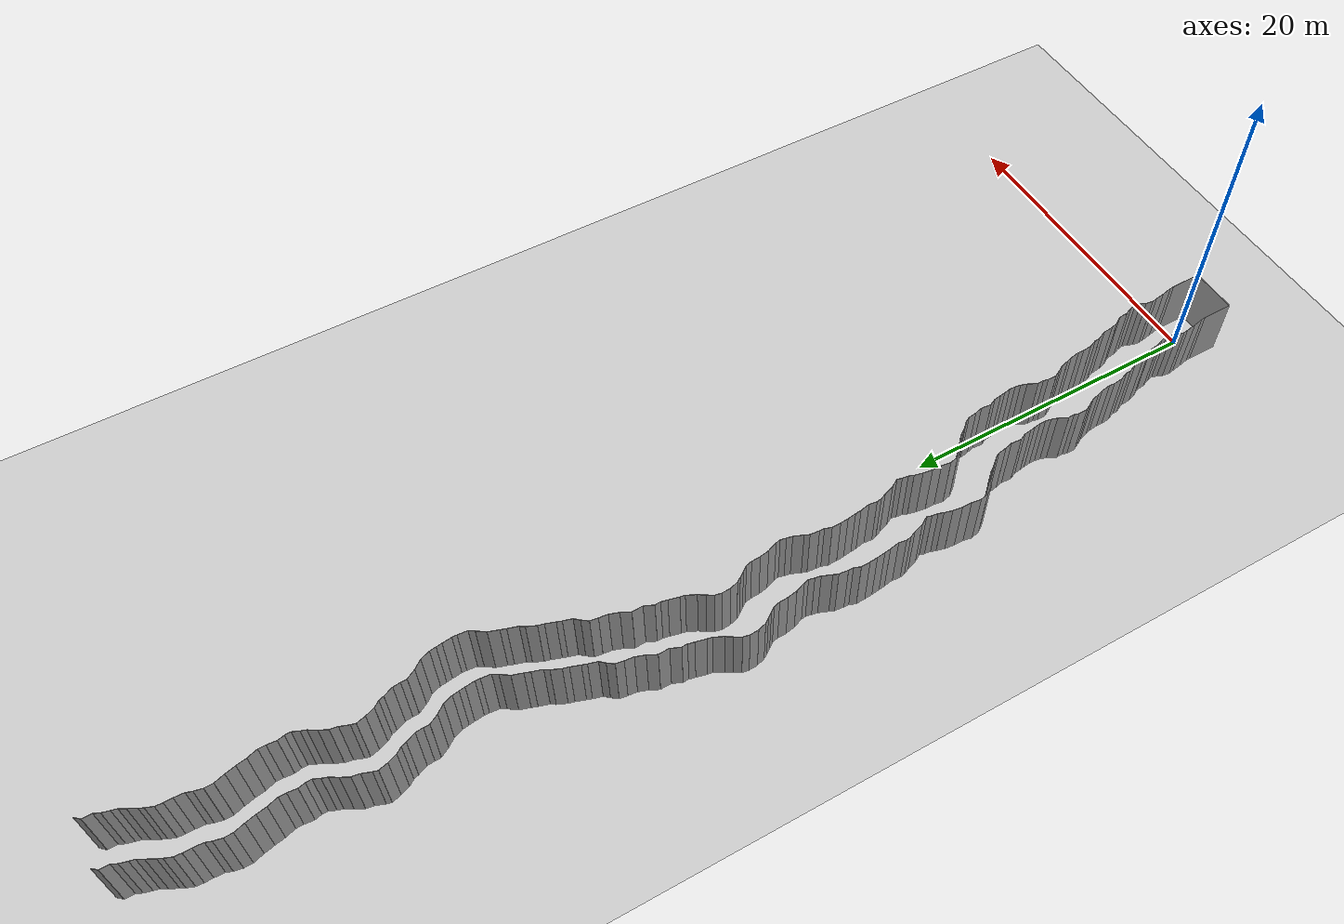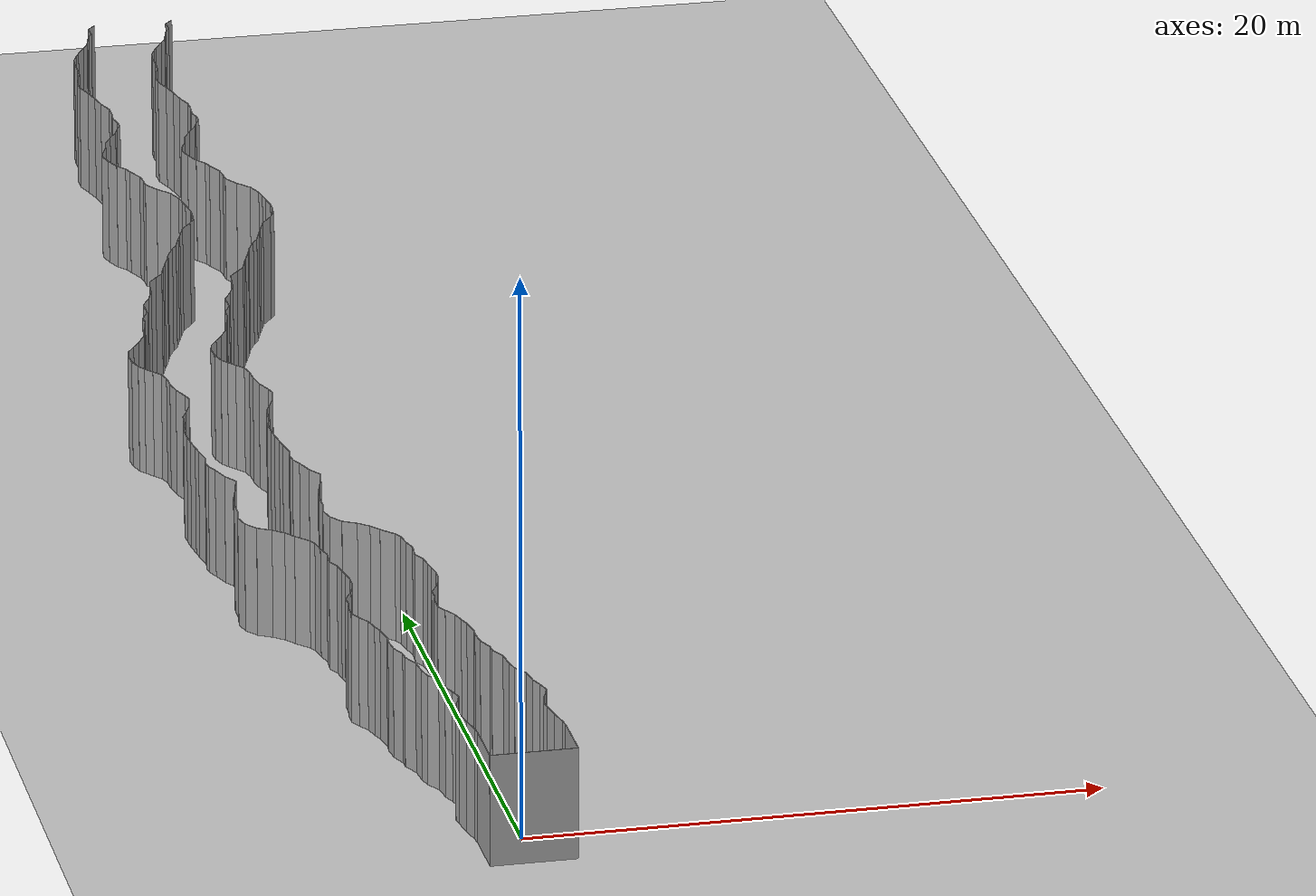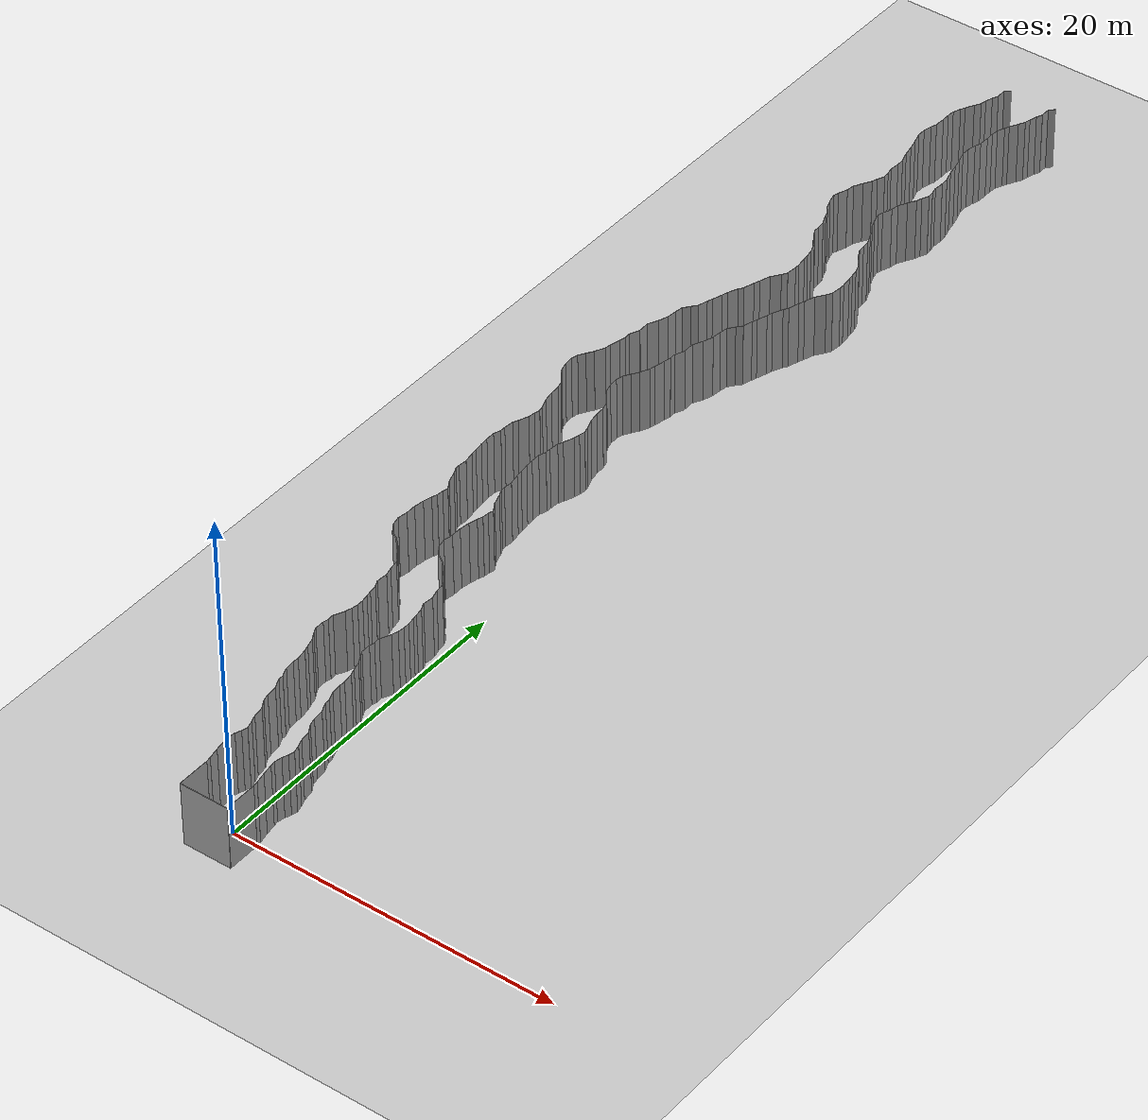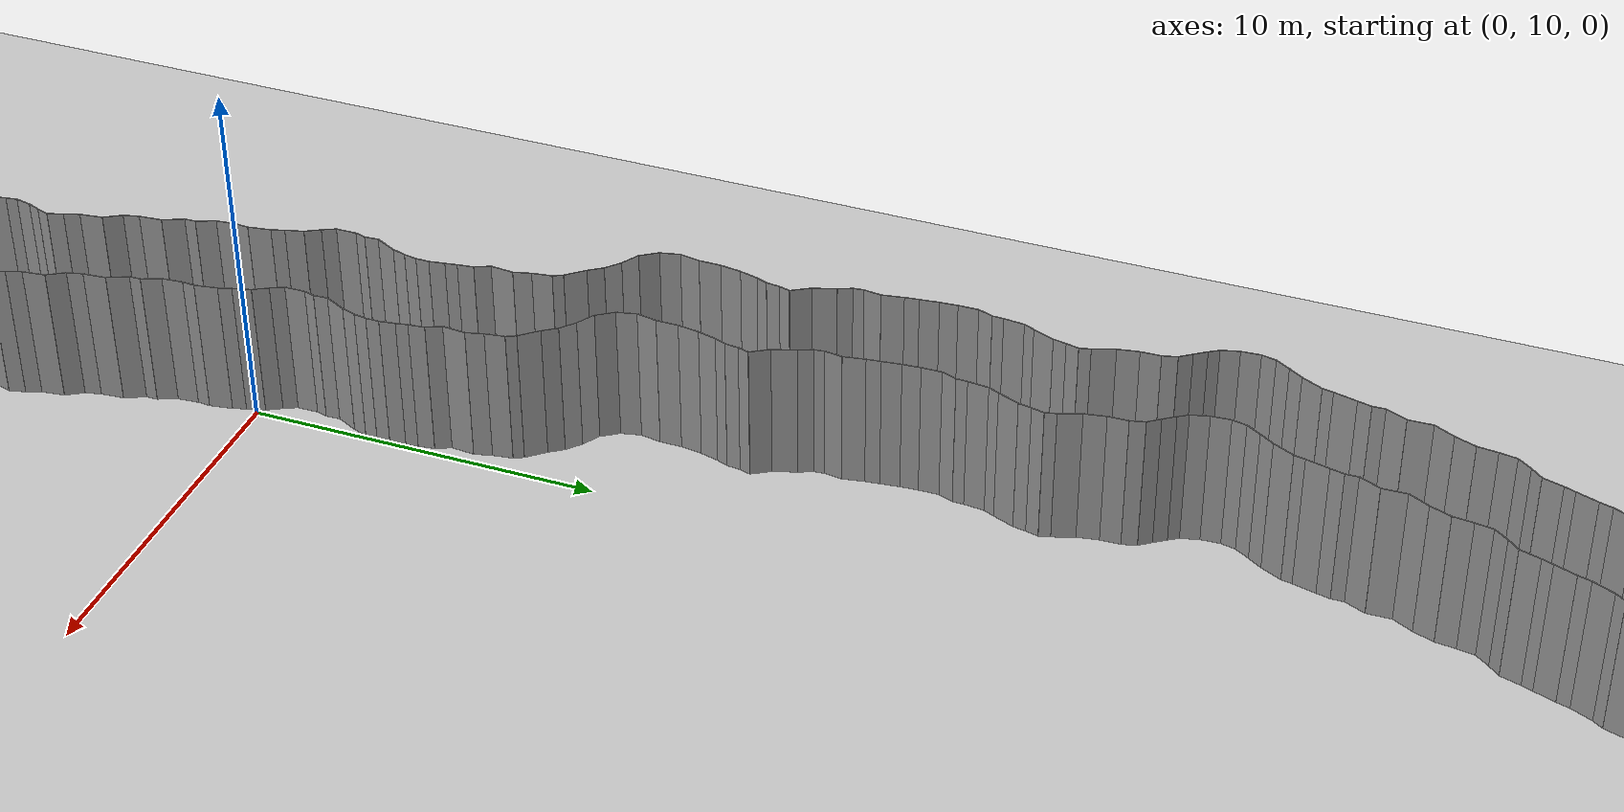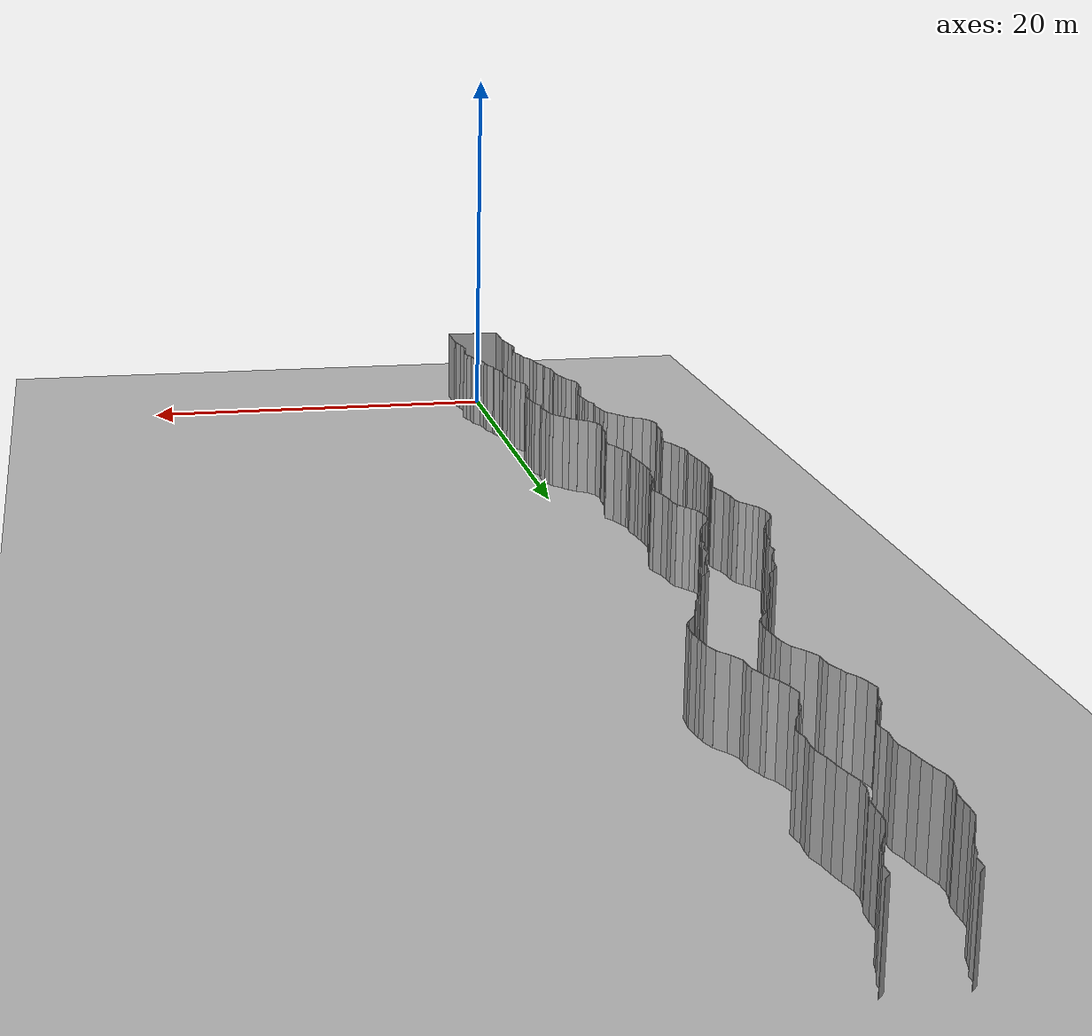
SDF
<sdf version="1.6">
 <world name="default">
  <light name="sun" type="directional">
   <pose>0 0 10 0 -0 0</pose>
   <diffuse>0.8 0.8 0.8 1</diffuse>
   <specular>0.2 0.2 0.2 1</specular>
   <attenuation>
    <range>1000</range>
    <constant>0.9</constant>
    <linear>0.01</linear>
    <quadratic>0.001</quadratic>
   </attenuation>
   <direction>-0.5 0.1 -0.9</direction>
  </light>
  <model name="ground_plane">
   <static>1</static>
   <link name="link">
    <collision name="collision">
     <geometry><plane><normal>0 0 1</normal><size>200 200</size></plane></geometry>
     <surface><friction><ode><mu>100</mu><mu2>50</mu2></ode></friction></surface>
    </collision>
    <visual name="visual">
     <cast_shadows>0</cast_shadows>
     <geometry><plane><normal>0 0 1</normal><size>200 200</size></plane></geometry>
     <material>
      <script><uri>file://media/materials/scripts/gazebo.material</uri><name>Gazebo/Grey</name></script>
     </material>
    </visual>
   </link>
   <pose>0 100 0 0 -0 0</pose>
  </model>
  <gravity>0 0 -9.8</gravity>
  <magnetic_field>6e-06 2.3e-05 -4.2e-05</magnetic_field>
  <atmosphere type="adiabatic"/>
  <physics default="0" name="default_physics" type="ode">
   <max_step_size>0.001</max_step_size>
   <real_time_factor>1</real_time_factor>
   <real_time_update_rate>1000</real_time_update_rate>
  </physics>
  <scene><ambient>0.4 0.4 0.4 1</ambient><background>0.7 0.7 0.7 1</background><shadows>0</shadows></scene>
  <spherical_coordinates>
   <surface_model>EARTH_WGS84</surface_model>
   <latitude_deg>0</latitude_deg>
   <longitude_deg>0</longitude_deg>
   <elevation>0</elevation>
   <heading_deg>0</heading_deg>
  </spherical_coordinates>
  <model name="wall_back">
   <static>1</static>
   <pose>0.0 -2 2 0.0 0 0.0</pose>
   <link name="link">
    <collision name="collision"><geometry><box><size>3 0.02 4</size></box></geometry></collision>
    <visual name="visual">
     <material>
      <script><name>Gazebo/Grey</name><uri>file://media/materials/scripts/gazebo.material</uri></script>
     </material>
     <geometry><box><size>3 0.02 4</size></box></geometry>
    </visual>
   </link>
  </model>
  <model name="wall_left">
   <static>1</static>
   <pose>1.5 -1 2 0 0 0.00</pose>
   <link name="link">
    <collision name="collision"><geometry><box><size>0.02 2 4</size></box></geometry></collision>
    <visual name="visual">
     <material>
      <script><name>Gazebo/Grey</name><uri>file://media/materials/scripts/gazebo.material</uri></script>
     </material>
     <geometry><box><size>0.02 2 4</size></box></geometry>
    </visual>
   </link>
  </model>
  <model name="wall_right">
   <static>1</static>
   <pose>-1.5 -1 2 0 0 0.00</pose>
   <link name="link">
    <collision name="collision"><geometry><box><size>0.02 2 4</size></box></geometry></collision>
    <visual name="visual">
     <material>
      <script><name>Gazebo/Grey</name><uri>file://media/materials/scripts/gazebo.material</uri></script>
     </material>
     <geometry><box><size>0.02 2 4</size></box></geometry>
    </visual>
   </link>
  </model>
  <model name="wall_0">
   <static>1</static>
   <pose>-1.51802748301 0.151666353413 2 0 0 0.118307690134</pose>
   <link name="link">
    <collision name="collision"><geometry><box><size>0.02 0.305467987857 4</size></box></geometry></collision>
    <visual name="visual">
     <material>
      <script><name>Gazebo/Grey</name><uri>file://media/materials/scripts/gazebo.material</uri></script>
     </material>
     <geometry><box><size>0.02 0.305467987857 4</size></box></geometry>
    </visual>
   </link>
  </model>
  <model name="wall_1">
   <static>1</static>
   <pose>1.48197251699 0.151666353413 2 0 0 0.118307690134</pose>
   <link name="link">
    <collision name="collision"><geometry><box><size>0.02 0.305467987857 4</size></box></geometry></collision>
    <visual name="visual">
     <material>
      <script><name>Gazebo/Grey</name><uri>file://media/materials/scripts/gazebo.material</uri></script>
     </material>
     <geometry><box><size>0.02 0.305467987857 4</size></box></geometry>
    </visual>
   </link>
  </model>
  <model name="wall_2">
   <static>1</static>
   <pose>-1.60328681057 0.641392963172 2 0 0 0.19631391145</pose>
   <link name="link">
    <collision name="collision"><geometry><box><size>0.02 0.689361611467 4</size></box></geometry></collision>
    <visual name="visual">
     <material>
      <script><name>Gazebo/Grey</name><uri>file://media/materials/scripts/gazebo.material</uri></script>
     </material>
     <geometry><box><size>0.02 0.689361611467 4</size></box></geometry>
    </visual>
   </link>
  </model>
  <model name="wall_3">
   <static>1</static>
   <pose>1.39671318943 0.641392963172 2 0 0 0.19631391145</pose>
   <link name="link">
    <collision name="collision"><geometry><box><size>0.02 0.689361611467 4</size></box></geometry></collision>
    <visual name="visual">
     <material>
      <script><name>Gazebo/Grey</name><uri>file://media/materials/scripts/gazebo.material</uri></script>
     </material>
     <geometry><box><size>0.02 0.689361611467 4</size></box></geometry>
    </visual>
   </link>
  </model>
  <model name="wall_4">
   <static>1</static>
   <pose>-1.72186030975 1.30952279659 2 0 0 0.154311375393</pose>
   <link name="link">
    <collision name="collision"><geometry><box><size>0.02 0.668077514084 4</size></box></geometry></collision>
    <visual name="visual">
     <material>
      <script><name>Gazebo/Grey</name><uri>file://media/materials/scripts/gazebo.material</uri></script>
     </material>
     <geometry><box><size>0.02 0.668077514084 4</size></box></geometry>
    </visual>
   </link>
  </model>
  <model name="wall_5">
   <static>1</static>
   <pose>1.27813969025 1.30952279659 2 0 0 0.154311375393</pose>
   <link name="link">
    <collision name="collision"><geometry><box><size>0.02 0.668077514084 4</size></box></geometry></collision>
    <visual name="visual">
     <material>
      <script><name>Gazebo/Grey</name><uri>file://media/materials/scripts/gazebo.material</uri></script>
     </material>
     <geometry><box><size>0.02 0.668077514084 4</size></box></geometry>
    </visual>
   </link>
  </model>
  <model name="wall_6">
   <static>1</static>
   <pose>-1.80035861939 1.80349740903 2 0 0 0.164193682765</pose>
   <link name="link">
    <collision name="collision"><geometry><box><size>0.02 0.332279066639 4</size></box></geometry></collision>
    <visual name="visual">
     <material>
      <script><name>Gazebo/Grey</name><uri>file://media/materials/scripts/gazebo.material</uri></script>
     </material>
     <geometry><box><size>0.02 0.332279066639 4</size></box></geometry>
    </visual>
   </link>
  </model>
  <model name="wall_7">
   <static>1</static>
   <pose>1.19964138061 1.80349740903 2 0 0 0.164193682765</pose>
   <link name="link">
    <collision name="collision"><geometry><box><size>0.02 0.332279066639 4</size></box></geometry></collision>
    <visual name="visual">
     <material>
      <script><name>Gazebo/Grey</name><uri>file://media/materials/scripts/gazebo.material</uri></script>
     </material>
     <geometry><box><size>0.02 0.332279066639 4</size></box></geometry>
    </visual>
   </link>
  </model>
  <model name="wall_8">
   <static>1</static>
   <pose>-1.78139266704 2.19385693883 2 0 0 -0.200924533399</pose>
   <link name="link">
    <collision name="collision"><geometry><box><size>0.02 0.4622074554 4</size></box></geometry></collision>
    <visual name="visual">
     <material>
      <script><name>Gazebo/Grey</name><uri>file://media/materials/scripts/gazebo.material</uri></script>
     </material>
     <geometry><box><size>0.02 0.4622074554 4</size></box></geometry>
    </visual>
   </link>
  </model>
  <model name="wall_9">
   <static>1</static>
   <pose>1.21860733296 2.19385693883 2 0 0 -0.200924533399</pose>
   <link name="link">
    <collision name="collision"><geometry><box><size>0.02 0.4622074554 4</size></box></geometry></collision>
    <visual name="visual">
     <material>
      <script><name>Gazebo/Grey</name><uri>file://media/materials/scripts/gazebo.material</uri></script>
     </material>
     <geometry><box><size>0.02 0.4622074554 4</size></box></geometry>
    </visual>
   </link>
  </model>
  <model name="wall_10">
   <static>1</static>
   <pose>-1.66700065461 2.59632746331 2 0 0 -0.36999640071</pose>
   <link name="link">
    <collision name="collision"><geometry><box><size>0.02 0.377583656975 4</size></box></geometry></collision>
    <visual name="visual">
     <material>
      <script><name>Gazebo/Grey</name><uri>file://media/materials/scripts/gazebo.material</uri></script>
     </material>
     <geometry><box><size>0.02 0.377583656975 4</size></box></geometry>
    </visual>
   </link>
  </model>
  <model name="wall_11">
   <static>1</static>
   <pose>1.33299934539 2.59632746331 2 0 0 -0.36999640071</pose>
   <link name="link">
    <collision name="collision"><geometry><box><size>0.02 0.377583656975 4</size></box></geometry></collision>
    <visual name="visual">
     <material>
      <script><name>Gazebo/Grey</name><uri>file://media/materials/scripts/gazebo.material</uri></script>
     </material>
     <geometry><box><size>0.02 0.377583656975 4</size></box></geometry>
    </visual>
   </link>
  </model>
  <model name="wall_12">
   <static>1</static>
   <pose>-1.54657020135 2.94392890397 2 0 0 -0.295117576943</pose>
   <link name="link">
    <collision name="collision"><geometry><box><size>0.02 0.35867717008 4</size></box></geometry></collision>
    <visual name="visual">
     <material>
      <script><name>Gazebo/Grey</name><uri>file://media/materials/scripts/gazebo.material</uri></script>
     </material>
     <geometry><box><size>0.02 0.35867717008 4</size></box></geometry>
    </visual>
   </link>
  </model>
  <model name="wall_13">
   <static>1</static>
   <pose>1.45342979865 2.94392890397 2 0 0 -0.295117576943</pose>
   <link name="link">
    <collision name="collision"><geometry><box><size>0.02 0.35867717008 4</size></box></geometry></collision>
    <visual name="visual">
     <material>
      <script><name>Gazebo/Grey</name><uri>file://media/materials/scripts/gazebo.material</uri></script>
     </material>
     <geometry><box><size>0.02 0.35867717008 4</size></box></geometry>
    </visual>
   </link>
  </model>
  <model name="wall_14">
   <static>1</static>
   <pose>-1.55528209008 3.34076347545 2 0 0 0.263942148788</pose>
   <link name="link">
    <collision name="collision"><geometry><box><size>0.02 0.466659185779 4</size></box></geometry></collision>
    <visual name="visual">
     <material>
      <script><name>Gazebo/Grey</name><uri>file://media/materials/scripts/gazebo.material</uri></script>
     </material>
     <geometry><box><size>0.02 0.466659185779 4</size></box></geometry>
    </visual>
   </link>
  </model>
  <model name="wall_15">
   <static>1</static>
   <pose>1.44471790992 3.34076347545 2 0 0 0.263942148788</pose>
   <link name="link">
    <collision name="collision"><geometry><box><size>0.02 0.466659185779 4</size></box></geometry></collision>
    <visual name="visual">
     <material>
      <script><name>Gazebo/Grey</name><uri>file://media/materials/scripts/gazebo.material</uri></script>
     </material>
     <geometry><box><size>0.02 0.466659185779 4</size></box></geometry>
    </visual>
   </link>
  </model>
  <model name="wall_16">
   <static>1</static>
   <pose>-1.69493595714 3.77816657191 2 0 0 0.355556754817</pose>
   <link name="link">
    <collision name="collision"><geometry><box><size>0.02 0.452617840314 4</size></box></geometry></collision>
    <visual name="visual">
     <material>
      <script><name>Gazebo/Grey</name><uri>file://media/materials/scripts/gazebo.material</uri></script>
     </material>
     <geometry><box><size>0.02 0.452617840314 4</size></box></geometry>
    </visual>
   </link>
  </model>
  <model name="wall_17">
   <static>1</static>
   <pose>1.30506404286 3.77816657191 2 0 0 0.355556754817</pose>
   <link name="link">
    <collision name="collision"><geometry><box><size>0.02 0.452617840314 4</size></box></geometry></collision>
    <visual name="visual">
     <material>
      <script><name>Gazebo/Grey</name><uri>file://media/materials/scripts/gazebo.material</uri></script>
     </material>
     <geometry><box><size>0.02 0.452617840314 4</size></box></geometry>
    </visual>
   </link>
  </model>
  <model name="wall_18">
   <static>1</static>
   <pose>-1.81481893491 4.31839089942 2 0 0 0.12463484553</pose>
   <link name="link">
    <collision name="collision"><geometry><box><size>0.02 0.661270172831 4</size></box></geometry></collision>
    <visual name="visual">
     <material>
      <script><name>Gazebo/Grey</name><uri>file://media/materials/scripts/gazebo.material</uri></script>
     </material>
     <geometry><box><size>0.02 0.661270172831 4</size></box></geometry>
    </visual>
   </link>
  </model>
  <model name="wall_19">
   <static>1</static>
   <pose>1.18518106509 4.31839089942 2 0 0 0.12463484553</pose>
   <link name="link">
    <collision name="collision"><geometry><box><size>0.02 0.661270172831 4</size></box></geometry></collision>
    <visual name="visual">
     <material>
      <script><name>Gazebo/Grey</name><uri>file://media/materials/scripts/gazebo.material</uri></script>
     </material>
     <geometry><box><size>0.02 0.661270172831 4</size></box></geometry>
    </visual>
   </link>
  </model>
  <model name="wall_20">
   <static>1</static>
   <pose>-2.00339153553 4.88723038613 2 0 0 0.549558450356</pose>
   <link name="link">
    <collision name="collision"><geometry><box><size>0.02 0.564685119379 4</size></box></geometry></collision>
    <visual name="visual">
     <material>
      <script><name>Gazebo/Grey</name><uri>file://media/materials/scripts/gazebo.material</uri></script>
     </material>
     <geometry><box><size>0.02 0.564685119379 4</size></box></geometry>
    </visual>
   </link>
  </model>
  <model name="wall_21">
   <static>1</static>
   <pose>0.99660846447 4.88723038613 2 0 0 0.549558450356</pose>
   <link name="link">
    <collision name="collision"><geometry><box><size>0.02 0.564685119379 4</size></box></geometry></collision>
    <visual name="visual">
     <material>
      <script><name>Gazebo/Grey</name><uri>file://media/materials/scripts/gazebo.material</uri></script>
     </material>
     <geometry><box><size>0.02 0.564685119379 4</size></box></geometry>
    </visual>
   </link>
  </model>
  <model name="wall_22">
   <static>1</static>
   <pose>-2.20555350939 5.35284562263 2 0 0 0.238605611034</pose>
   <link name="link">
    <collision name="collision"><geometry><box><size>0.02 0.46280423056 4</size></box></geometry></collision>
    <visual name="visual">
     <material>
      <script><name>Gazebo/Grey</name><uri>file://media/materials/scripts/gazebo.material</uri></script>
     </material>
     <geometry><box><size>0.02 0.46280423056 4</size></box></geometry>
    </visual>
   </link>
  </model>
  <model name="wall_23">
   <static>1</static>
   <pose>0.794446490612 5.35284562263 2 0 0 0.238605611034</pose>
   <link name="link">
    <collision name="collision"><geometry><box><size>0.02 0.46280423056 4</size></box></geometry></collision>
    <visual name="visual">
     <material>
      <script><name>Gazebo/Grey</name><uri>file://media/materials/scripts/gazebo.material</uri></script>
     </material>
     <geometry><box><size>0.02 0.46280423056 4</size></box></geometry>
    </visual>
   </link>
  </model>
  <model name="wall_24">
   <static>1</static>
   <pose>-2.28925769092 5.90601313707 2 0 0 0.0881380179179</pose>
   <link name="link">
    <collision name="collision"><geometry><box><size>0.02 0.659201529352 4</size></box></geometry></collision>
    <visual name="visual">
     <material>
      <script><name>Gazebo/Grey</name><uri>file://media/materials/scripts/gazebo.material</uri></script>
     </material>
     <geometry><box><size>0.02 0.659201529352 4</size></box></geometry>
    </visual>
   </link>
  </model>
  <model name="wall_25">
   <static>1</static>
   <pose>0.71074230908 5.90601313707 2 0 0 0.0881380179179</pose>
   <link name="link">
    <collision name="collision"><geometry><box><size>0.02 0.659201529352 4</size></box></geometry></collision>
    <visual name="visual">
     <material>
      <script><name>Gazebo/Grey</name><uri>file://media/materials/scripts/gazebo.material</uri></script>
     </material>
     <geometry><box><size>0.02 0.659201529352 4</size></box></geometry>
    </visual>
   </link>
  </model>
  <model name="wall_26">
   <static>1</static>
   <pose>-2.4486799668 6.52444426609 2 0 0 0.422452901165</pose>
   <link name="link">
    <collision name="collision"><geometry><box><size>0.02 0.636145619652 4</size></box></geometry></collision>
    <visual name="visual">
     <material>
      <script><name>Gazebo/Grey</name><uri>file://media/materials/scripts/gazebo.material</uri></script>
     </material>
     <geometry><box><size>0.02 0.636145619652 4</size></box></geometry>
    </visual>
   </link>
  </model>
  <model name="wall_27">
   <static>1</static>
   <pose>0.551320033198 6.52444426609 2 0 0 0.422452901165</pose>
   <link name="link">
    <collision name="collision"><geometry><box><size>0.02 0.636145619652 4</size></box></geometry></collision>
    <visual name="visual">
     <material>
      <script><name>Gazebo/Grey</name><uri>file://media/materials/scripts/gazebo.material</uri></script>
     </material>
     <geometry><box><size>0.02 0.636145619652 4</size></box></geometry>
    </visual>
   </link>
  </model>
  <model name="wall_28">
   <static>1</static>
   <pose>-2.58313098686 6.97634690997 2 0 0 0.024974302816</pose>
   <link name="link">
    <collision name="collision"><geometry><box><size>0.02 0.323686714192 4</size></box></geometry></collision>
    <visual name="visual">
     <material>
      <script><name>Gazebo/Grey</name><uri>file://media/materials/scripts/gazebo.material</uri></script>
     </material>
     <geometry><box><size>0.02 0.323686714192 4</size></box></geometry>
    </visual>
   </link>
  </model>
  <model name="wall_29">
   <static>1</static>
   <pose>0.41686901314 6.97634690997 2 0 0 0.024974302816</pose>
   <link name="link">
    <collision name="collision"><geometry><box><size>0.02 0.323686714192 4</size></box></geometry></collision>
    <visual name="visual">
     <material>
      <script><name>Gazebo/Grey</name><uri>file://media/materials/scripts/gazebo.material</uri></script>
     </material>
     <geometry><box><size>0.02 0.323686714192 4</size></box></geometry>
    </visual>
   </link>
  </model>
  <model name="wall_30">
   <static>1</static>
   <pose>-2.69502833746 7.40506672146 2 0 0 0.384005826739</pose>
   <link name="link">
    <collision name="collision"><geometry><box><size>0.02 0.575787690601 4</size></box></geometry></collision>
    <visual name="visual">
     <material>
      <script><name>Gazebo/Grey</name><uri>file://media/materials/scripts/gazebo.material</uri></script>
     </material>
     <geometry><box><size>0.02 0.575787690601 4</size></box></geometry>
    </visual>
   </link>
  </model>
  <model name="wall_31">
   <static>1</static>
   <pose>0.304971662536 7.40506672146 2 0 0 0.384005826739</pose>
   <link name="link">
    <collision name="collision"><geometry><box><size>0.02 0.575787690601 4</size></box></geometry></collision>
    <visual name="visual">
     <material>
      <script><name>Gazebo/Grey</name><uri>file://media/materials/scripts/gazebo.material</uri></script>
     </material>
     <geometry><box><size>0.02 0.575787690601 4</size></box></geometry>
    </visual>
   </link>
  </model>
  <model name="wall_32">
   <static>1</static>
   <pose>-2.83111612573 7.97242648465 2 0 0 0.0936957462048</pose>
   <link name="link">
    <collision name="collision"><geometry><box><size>0.02 0.60351282839 4</size></box></geometry></collision>
    <visual name="visual">
     <material>
      <script><name>Gazebo/Grey</name><uri>file://media/materials/scripts/gazebo.material</uri></script>
     </material>
     <geometry><box><size>0.02 0.60351282839 4</size></box></geometry>
    </visual>
   </link>
  </model>
  <model name="wall_33">
   <static>1</static>
   <pose>0.168883874265 7.97242648465 2 0 0 0.0936957462048</pose>
   <link name="link">
    <collision name="collision"><geometry><box><size>0.02 0.60351282839 4</size></box></geometry></collision>
    <visual name="visual">
     <material>
      <script><name>Gazebo/Grey</name><uri>file://media/materials/scripts/gazebo.material</uri></script>
     </material>
     <geometry><box><size>0.02 0.60351282839 4</size></box></geometry>
    </visual>
   </link>
  </model>
  <model name="wall_34">
   <static>1</static>
   <pose>-2.84560137236 8.45178050341 2 0 0 -0.0766803706387</pose>
   <link name="link">
    <collision name="collision"><geometry><box><size>0.02 0.35889697747 4</size></box></geometry></collision>
    <visual name="visual">
     <material>
      <script><name>Gazebo/Grey</name><uri>file://media/materials/scripts/gazebo.material</uri></script>
     </material>
     <geometry><box><size>0.02 0.35889697747 4</size></box></geometry>
    </visual>
   </link>
  </model>
  <model name="wall_35">
   <static>1</static>
   <pose>0.154398627639 8.45178050341 2 0 0 -0.0766803706387</pose>
   <link name="link">
    <collision name="collision"><geometry><box><size>0.02 0.35889697747 4</size></box></geometry></collision>
    <visual name="visual">
     <material>
      <script><name>Gazebo/Grey</name><uri>file://media/materials/scripts/gazebo.material</uri></script>
     </material>
     <geometry><box><size>0.02 0.35889697747 4</size></box></geometry>
    </visual>
   </link>
  </model>
  <model name="wall_36">
   <static>1</static>
   <pose>-2.88339367317 8.95742810442 2 0 0 0.156454397341</pose>
   <link name="link">
    <collision name="collision"><geometry><box><size>0.02 0.661532834291 4</size></box></geometry></collision>
    <visual name="visual">
     <material>
      <script><name>Gazebo/Grey</name><uri>file://media/materials/scripts/gazebo.material</uri></script>
     </material>
     <geometry><box><size>0.02 0.661532834291 4</size></box></geometry>
    </visual>
   </link>
  </model>
  <model name="wall_37">
   <static>1</static>
   <pose>0.116606326832 8.95742810442 2 0 0 0.156454397341</pose>
   <link name="link">
    <collision name="collision"><geometry><box><size>0.02 0.661532834291 4</size></box></geometry></collision>
    <visual name="visual">
     <material>
      <script><name>Gazebo/Grey</name><uri>file://media/materials/scripts/gazebo.material</uri></script>
     </material>
     <geometry><box><size>0.02 0.661532834291 4</size></box></geometry>
    </visual>
   </link>
  </model>
  <model name="wall_38">
   <static>1</static>
   <pose>-2.99266797859 9.46782981925 2 0 0 0.304554426678</pose>
   <link name="link">
    <collision name="collision"><geometry><box><size>0.02 0.385071314135 4</size></box></geometry></collision>
    <visual name="visual">
     <material>
      <script><name>Gazebo/Grey</name><uri>file://media/materials/scripts/gazebo.material</uri></script>
     </material>
     <geometry><box><size>0.02 0.385071314135 4</size></box></geometry>
    </visual>
   </link>
  </model>
  <model name="wall_39">
   <static>1</static>
   <pose>0.0073320214051 9.46782981925 2 0 0 0.304554426678</pose>
   <link name="link">
    <collision name="collision"><geometry><box><size>0.02 0.385071314135 4</size></box></geometry></collision>
    <visual name="visual">
     <material>
      <script><name>Gazebo/Grey</name><uri>file://media/materials/scripts/gazebo.material</uri></script>
     </material>
     <geometry><box><size>0.02 0.385071314135 4</size></box></geometry>
    </visual>
   </link>
  </model>
  <model name="wall_40">
   <static>1</static>
   <pose>-3.1178512269 9.90898755364 2 0 0 0.256195221433</pose>
   <link name="link">
    <collision name="collision"><geometry><box><size>0.02 0.532339861456 4</size></box></geometry></collision>
    <visual name="visual">
     <material>
      <script><name>Gazebo/Grey</name><uri>file://media/materials/scripts/gazebo.material</uri></script>
     </material>
     <geometry><box><size>0.02 0.532339861456 4</size></box></geometry>
    </visual>
   </link>
  </model>
  <model name="wall_41">
   <static>1</static>
   <pose>-0.117851226898 9.90898755364 2 0 0 0.256195221433</pose>
   <link name="link">
    <collision name="collision"><geometry><box><size>0.02 0.532339861456 4</size></box></geometry></collision>
    <visual name="visual">
     <material>
      <script><name>Gazebo/Grey</name><uri>file://media/materials/scripts/gazebo.material</uri></script>
     </material>
     <geometry><box><size>0.02 0.532339861456 4</size></box></geometry>
    </visual>
   </link>
  </model>
  <model name="wall_42">
   <static>1</static>
   <pose>-3.30201148022 10.3719976853 2 0 0 0.516456826404</pose>
   <link name="link">
    <collision name="collision"><geometry><box><size>0.02 0.472708772016 4</size></box></geometry></collision>
    <visual name="visual">
     <material>
      <script><name>Gazebo/Grey</name><uri>file://media/materials/scripts/gazebo.material</uri></script>
     </material>
     <geometry><box><size>0.02 0.472708772016 4</size></box></geometry>
    </visual>
   </link>
  </model>
  <model name="wall_43">
   <static>1</static>
   <pose>-0.30201148022 10.3719976853 2 0 0 0.516456826404</pose>
   <link name="link">
    <collision name="collision"><geometry><box><size>0.02 0.472708772016 4</size></box></geometry></collision>
    <visual name="visual">
     <material>
      <script><name>Gazebo/Grey</name><uri>file://media/materials/scripts/gazebo.material</uri></script>
     </material>
     <geometry><box><size>0.02 0.472708772016 4</size></box></geometry>
    </visual>
   </link>
  </model>
  <model name="wall_44">
   <static>1</static>
   <pose>-3.51064375005 10.7627205591 2 0 0 0.460716099515</pose>
   <link name="link">
    <collision name="collision"><geometry><box><size>0.02 0.413504699785 4</size></box></geometry></collision>
    <visual name="visual">
     <material>
      <script><name>Gazebo/Grey</name><uri>file://media/materials/scripts/gazebo.material</uri></script>
     </material>
     <geometry><box><size>0.02 0.413504699785 4</size></box></geometry>
    </visual>
   </link>
  </model>
  <model name="wall_45">
   <static>1</static>
   <pose>-0.510643750047 10.7627205591 2 0 0 0.460716099515</pose>
   <link name="link">
    <collision name="collision"><geometry><box><size>0.02 0.413504699785 4</size></box></geometry></collision>
    <visual name="visual">
     <material>
      <script><name>Gazebo/Grey</name><uri>file://media/materials/scripts/gazebo.material</uri></script>
     </material>
     <geometry><box><size>0.02 0.413504699785 4</size></box></geometry>
    </visual>
   </link>
  </model>
  <model name="wall_46">
   <static>1</static>
   <pose>-3.60495940068 11.2461868546 2 0 0 0.0080317635055</pose>
   <link name="link">
    <collision name="collision"><geometry><box><size>0.02 0.596561466439 4</size></box></geometry></collision>
    <visual name="visual">
     <material>
      <script><name>Gazebo/Grey</name><uri>file://media/materials/scripts/gazebo.material</uri></script>
     </material>
     <geometry><box><size>0.02 0.596561466439 4</size></box></geometry>
    </visual>
   </link>
  </model>
  <model name="wall_47">
   <static>1</static>
   <pose>-0.60495940068 11.2461868546 2 0 0 0.0080317635055</pose>
   <link name="link">
    <collision name="collision"><geometry><box><size>0.02 0.596561466439 4</size></box></geometry></collision>
    <visual name="visual">
     <material>
      <script><name>Gazebo/Grey</name><uri>file://media/materials/scripts/gazebo.material</uri></script>
     </material>
     <geometry><box><size>0.02 0.596561466439 4</size></box></geometry>
    </visual>
   </link>
  </model>
  <model name="wall_48">
   <static>1</static>
   <pose>-3.56547380532 11.6974473287 2 0 0 -0.267206474128</pose>
   <link name="link">
    <collision name="collision"><geometry><box><size>0.02 0.317236739746 4</size></box></geometry></collision>
    <visual name="visual">
     <material>
      <script><name>Gazebo/Grey</name><uri>file://media/materials/scripts/gazebo.material</uri></script>
     </material>
     <geometry><box><size>0.02 0.317236739746 4</size></box></geometry>
    </visual>
   </link>
  </model>
  <model name="wall_49">
   <static>1</static>
   <pose>-0.565473805317 11.6974473287 2 0 0 -0.267206474128</pose>
   <link name="link">
    <collision name="collision"><geometry><box><size>0.02 0.317236739746 4</size></box></geometry></collision>
    <visual name="visual">
     <material>
      <script><name>Gazebo/Grey</name><uri>file://media/materials/scripts/gazebo.material</uri></script>
     </material>
     <geometry><box><size>0.02 0.317236739746 4</size></box></geometry>
    </visual>
   </link>
  </model>
  <model name="wall_50">
   <static>1</static>
   <pose>-3.5349618703 12.0516624276 2 0 0 0.0564404932744</pose>
   <link name="link">
    <collision name="collision"><geometry><box><size>0.02 0.403093336625 4</size></box></geometry></collision>
    <visual name="visual">
     <material>
      <script><name>Gazebo/Grey</name><uri>file://media/materials/scripts/gazebo.material</uri></script>
     </material>
     <geometry><box><size>0.02 0.403093336625 4</size></box></geometry>
    </visual>
   </link>
  </model>
  <model name="wall_51">
   <static>1</static>
   <pose>-0.534961870301 12.0516624276 2 0 0 0.0564404932744</pose>
   <link name="link">
    <collision name="collision"><geometry><box><size>0.02 0.403093336625 4</size></box></geometry></collision>
    <visual name="visual">
     <material>
      <script><name>Gazebo/Grey</name><uri>file://media/materials/scripts/gazebo.material</uri></script>
     </material>
     <geometry><box><size>0.02 0.403093336625 4</size></box></geometry>
    </visual>
   </link>
  </model>
  <model name="wall_52">
   <static>1</static>
   <pose>-3.39544558827 12.5559183652 2 0 0 -0.461984444909</pose>
   <link name="link">
    <collision name="collision"><geometry><box><size>0.02 0.677034054802 4</size></box></geometry></collision>
    <visual name="visual">
     <material>
      <script><name>Gazebo/Grey</name><uri>file://media/materials/scripts/gazebo.material</uri></script>
     </material>
     <geometry><box><size>0.02 0.677034054802 4</size></box></geometry>
    </visual>
   </link>
  </model>
  <model name="wall_53">
   <static>1</static>
   <pose>-0.395445588269 12.5559183652 2 0 0 -0.461984444909</pose>
   <link name="link">
    <collision name="collision"><geometry><box><size>0.02 0.677034054802 4</size></box></geometry></collision>
    <visual name="visual">
     <material>
      <script><name>Gazebo/Grey</name><uri>file://media/materials/scripts/gazebo.material</uri></script>
     </material>
     <geometry><box><size>0.02 0.677034054802 4</size></box></geometry>
    </visual>
   </link>
  </model>
  <model name="wall_54">
   <static>1</static>
   <pose>-3.18357437276 13.0579258436 2 0 0 -0.297404980701</pose>
   <link name="link">
    <collision name="collision"><geometry><box><size>0.02 0.416226851161 4</size></box></geometry></collision>
    <visual name="visual">
     <material>
      <script><name>Gazebo/Grey</name><uri>file://media/materials/scripts/gazebo.material</uri></script>
     </material>
     <geometry><box><size>0.02 0.416226851161 4</size></box></geometry>
    </visual>
   </link>
  </model>
  <model name="wall_55">
   <static>1</static>
   <pose>-0.183574372758 13.0579258436 2 0 0 -0.297404980701</pose>
   <link name="link">
    <collision name="collision"><geometry><box><size>0.02 0.416226851161 4</size></box></geometry></collision>
    <visual name="visual">
     <material>
      <script><name>Gazebo/Grey</name><uri>file://media/materials/scripts/gazebo.material</uri></script>
     </material>
     <geometry><box><size>0.02 0.416226851161 4</size></box></geometry>
    </visual>
   </link>
  </model>
  <model name="wall_56">
   <static>1</static>
   <pose>-3.09158096186 13.4420219869 2 0 0 -0.165961597693</pose>
   <link name="link">
    <collision name="collision"><geometry><box><size>0.02 0.375395684745 4</size></box></geometry></collision>
    <visual name="visual">
     <material>
      <script><name>Gazebo/Grey</name><uri>file://media/materials/scripts/gazebo.material</uri></script>
     </material>
     <geometry><box><size>0.02 0.375395684745 4</size></box></geometry>
    </visual>
   </link>
  </model>
  <model name="wall_57">
   <static>1</static>
   <pose>-0.0915809618615 13.4420219869 2 0 0 -0.165961597693</pose>
   <link name="link">
    <collision name="collision"><geometry><box><size>0.02 0.375395684745 4</size></box></geometry></collision>
    <visual name="visual">
     <material>
      <script><name>Gazebo/Grey</name><uri>file://media/materials/scripts/gazebo.material</uri></script>
     </material>
     <geometry><box><size>0.02 0.375395684745 4</size></box></geometry>
    </visual>
   </link>
  </model>
  <model name="wall_58">
   <static>1</static>
   <pose>-3.05793368652 13.8198006716 2 0 0 -0.0136991611717</pose>
   <link name="link">
    <collision name="collision"><geometry><box><size>0.02 0.385355796973 4</size></box></geometry></collision>
    <visual name="visual">
     <material>
      <script><name>Gazebo/Grey</name><uri>file://media/materials/scripts/gazebo.material</uri></script>
     </material>
     <geometry><box><size>0.02 0.385355796973 4</size></box></geometry>
    </visual>
   </link>
  </model>
  <model name="wall_59">
   <static>1</static>
   <pose>-0.0579336865197 13.8198006716 2 0 0 -0.0136991611717</pose>
   <link name="link">
    <collision name="collision"><geometry><box><size>0.02 0.385355796973 4</size></box></geometry></collision>
    <visual name="visual">
     <material>
      <script><name>Gazebo/Grey</name><uri>file://media/materials/scripts/gazebo.material</uri></script>
     </material>
     <geometry><box><size>0.02 0.385355796973 4</size></box></geometry>
    </visual>
   </link>
  </model>
  <model name="wall_60">
   <static>1</static>
   <pose>-3.0911898536 14.2349193411 2 0 0 0.159979499789</pose>
   <link name="link">
    <collision name="collision"><geometry><box><size>0.02 0.450672541682 4</size></box></geometry></collision>
    <visual name="visual">
     <material>
      <script><name>Gazebo/Grey</name><uri>file://media/materials/scripts/gazebo.material</uri></script>
     </material>
     <geometry><box><size>0.02 0.450672541682 4</size></box></geometry>
    </visual>
   </link>
  </model>
  <model name="wall_61">
   <static>1</static>
   <pose>-0.0911898536017 14.2349193411 2 0 0 0.159979499789</pose>
   <link name="link">
    <collision name="collision"><geometry><box><size>0.02 0.450672541682 4</size></box></geometry></collision>
    <visual name="visual">
     <material>
      <script><name>Gazebo/Grey</name><uri>file://media/materials/scripts/gazebo.material</uri></script>
     </material>
     <geometry><box><size>0.02 0.450672541682 4</size></box></geometry>
    </visual>
   </link>
  </model>
  <model name="wall_62">
   <static>1</static>
   <pose>-3.15537241516 14.6273096099 2 0 0 0.164948549006</pose>
   <link name="link">
    <collision name="collision"><geometry><box><size>0.02 0.344539336259 4</size></box></geometry></collision>
    <visual name="visual">
     <material>
      <script><name>Gazebo/Grey</name><uri>file://media/materials/scripts/gazebo.material</uri></script>
     </material>
     <geometry><box><size>0.02 0.344539336259 4</size></box></geometry>
    </visual>
   </link>
  </model>
  <model name="wall_63">
   <static>1</static>
   <pose>-0.155372415158 14.6273096099 2 0 0 0.164948549006</pose>
   <link name="link">
    <collision name="collision"><geometry><box><size>0.02 0.344539336259 4</size></box></geometry></collision>
    <visual name="visual">
     <material>
      <script><name>Gazebo/Grey</name><uri>file://media/materials/scripts/gazebo.material</uri></script>
     </material>
     <geometry><box><size>0.02 0.344539336259 4</size></box></geometry>
    </visual>
   </link>
  </model>
  <model name="wall_64">
   <static>1</static>
   <pose>-3.21179401468 15.028823684 2 0 0 0.12089611564</pose>
   <link name="link">
    <collision name="collision"><geometry><box><size>0.02 0.466570830097 4</size></box></geometry></collision>
    <visual name="visual">
     <material>
      <script><name>Gazebo/Grey</name><uri>file://media/materials/scripts/gazebo.material</uri></script>
     </material>
     <geometry><box><size>0.02 0.466570830097 4</size></box></geometry>
    </visual>
   </link>
  </model>
  <model name="wall_65">
   <static>1</static>
   <pose>-0.211794014676 15.028823684 2 0 0 0.12089611564</pose>
   <link name="link">
    <collision name="collision"><geometry><box><size>0.02 0.466570830097 4</size></box></geometry></collision>
    <visual name="visual">
     <material>
      <script><name>Gazebo/Grey</name><uri>file://media/materials/scripts/gazebo.material</uri></script>
     </material>
     <geometry><box><size>0.02 0.466570830097 4</size></box></geometry>
    </visual>
   </link>
  </model>
  <model name="wall_66">
   <static>1</static>
   <pose>-3.34022064705 15.4723174604 2 0 0 0.442038981665</pose>
   <link name="link">
    <collision name="collision"><geometry><box><size>0.02 0.468891480701 4</size></box></geometry></collision>
    <visual name="visual">
     <material>
      <script><name>Gazebo/Grey</name><uri>file://media/materials/scripts/gazebo.material</uri></script>
     </material>
     <geometry><box><size>0.02 0.468891480701 4</size></box></geometry>
    </visual>
   </link>
  </model>
  <model name="wall_67">
   <static>1</static>
   <pose>-0.340220647049 15.4723174604 2 0 0 0.442038981665</pose>
   <link name="link">
    <collision name="collision"><geometry><box><size>0.02 0.468891480701 4</size></box></geometry></collision>
    <visual name="visual">
     <material>
      <script><name>Gazebo/Grey</name><uri>file://media/materials/scripts/gazebo.material</uri></script>
     </material>
     <geometry><box><size>0.02 0.468891480701 4</size></box></geometry>
    </visual>
   </link>
  </model>
  <model name="wall_68">
   <static>1</static>
   <pose>-3.41192526054 16.0178841337 2 0 0 -0.085470552933</pose>
   <link name="link">
    <collision name="collision"><geometry><box><size>0.02 0.669755972355 4</size></box></geometry></collision>
    <visual name="visual">
     <material>
      <script><name>Gazebo/Grey</name><uri>file://media/materials/scripts/gazebo.material</uri></script>
     </material>
     <geometry><box><size>0.02 0.669755972355 4</size></box></geometry>
    </visual>
   </link>
  </model>
  <model name="wall_69">
   <static>1</static>
   <pose>-0.411925260545 16.0178841337 2 0 0 -0.085470552933</pose>
   <link name="link">
    <collision name="collision"><geometry><box><size>0.02 0.669755972355 4</size></box></geometry></collision>
    <visual name="visual">
     <material>
      <script><name>Gazebo/Grey</name><uri>file://media/materials/scripts/gazebo.material</uri></script>
     </material>
     <geometry><box><size>0.02 0.669755972355 4</size></box></geometry>
    </visual>
   </link>
  </model>
  <model name="wall_70">
   <static>1</static>
   <pose>-3.44881021815 16.5997536387 2 0 0 0.257899608758</pose>
   <link name="link">
    <collision name="collision"><geometry><box><size>0.02 0.513407408962 4</size></box></geometry></collision>
    <visual name="visual">
     <material>
      <script><name>Gazebo/Grey</name><uri>file://media/materials/scripts/gazebo.material</uri></script>
     </material>
     <geometry><box><size>0.02 0.513407408962 4</size></box></geometry>
    </visual>
   </link>
  </model>
  <model name="wall_71">
   <static>1</static>
   <pose>-0.448810218151 16.5997536387 2 0 0 0.257899608758</pose>
   <link name="link">
    <collision name="collision"><geometry><box><size>0.02 0.513407408962 4</size></box></geometry></collision>
    <visual name="visual">
     <material>
      <script><name>Gazebo/Grey</name><uri>file://media/materials/scripts/gazebo.material</uri></script>
     </material>
     <geometry><box><size>0.02 0.513407408962 4</size></box></geometry>
    </visual>
   </link>
  </model>
  <model name="wall_72">
   <static>1</static>
   <pose>-3.5559207074 17.1305444143 2 0 0 0.146298872248</pose>
   <link name="link">
    <collision name="collision"><geometry><box><size>0.02 0.571256150958 4</size></box></geometry></collision>
    <visual name="visual">
     <material>
      <script><name>Gazebo/Grey</name><uri>file://media/materials/scripts/gazebo.material</uri></script>
     </material>
     <geometry><box><size>0.02 0.571256150958 4</size></box></geometry>
    </visual>
   </link>
  </model>
  <model name="wall_73">
   <static>1</static>
   <pose>-0.555920707397 17.1305444143 2 0 0 0.146298872248</pose>
   <link name="link">
    <collision name="collision"><geometry><box><size>0.02 0.571256150958 4</size></box></geometry></collision>
    <visual name="visual">
     <material>
      <script><name>Gazebo/Grey</name><uri>file://media/materials/scripts/gazebo.material</uri></script>
     </material>
     <geometry><box><size>0.02 0.571256150958 4</size></box></geometry>
    </visual>
   </link>
  </model>
  <model name="wall_74">
   <static>1</static>
   <pose>-3.66425128231 17.5491208052 2 0 0 0.455927642203</pose>
   <link name="link">
    <collision name="collision"><geometry><box><size>0.02 0.302943958457 4</size></box></geometry></collision>
    <visual name="visual">
     <material>
      <script><name>Gazebo/Grey</name><uri>file://media/materials/scripts/gazebo.material</uri></script>
     </material>
     <geometry><box><size>0.02 0.302943958457 4</size></box></geometry>
    </visual>
   </link>
  </model>
  <model name="wall_75">
   <static>1</static>
   <pose>-0.664251282315 17.5491208052 2 0 0 0.455927642203</pose>
   <link name="link">
    <collision name="collision"><geometry><box><size>0.02 0.302943958457 4</size></box></geometry></collision>
    <visual name="visual">
     <material>
      <script><name>Gazebo/Grey</name><uri>file://media/materials/scripts/gazebo.material</uri></script>
     </material>
     <geometry><box><size>0.02 0.302943958457 4</size></box></geometry>
    </visual>
   </link>
  </model>
  <model name="wall_76">
   <static>1</static>
   <pose>-3.94526130173 17.932122336 2 0 0 0.714666645023</pose>
   <link name="link">
    <collision name="collision"><geometry><box><size>0.02 0.65403977165 4</size></box></geometry></collision>
    <visual name="visual">
     <material>
      <script><name>Gazebo/Grey</name><uri>file://media/materials/scripts/gazebo.material</uri></script>
     </material>
     <geometry><box><size>0.02 0.65403977165 4</size></box></geometry>
    </visual>
   </link>
  </model>
  <model name="wall_77">
   <static>1</static>
   <pose>-0.945261301727 17.932122336 2 0 0 0.714666645023</pose>
   <link name="link">
    <collision name="collision"><geometry><box><size>0.02 0.65403977165 4</size></box></geometry></collision>
    <visual name="visual">
     <material>
      <script><name>Gazebo/Grey</name><uri>file://media/materials/scripts/gazebo.material</uri></script>
     </material>
     <geometry><box><size>0.02 0.65403977165 4</size></box></geometry>
    </visual>
   </link>
  </model>
  <model name="wall_78">
   <static>1</static>
   <pose>-4.29549473867 18.3744088981 2 0 0 0.608028593425</pose>
   <link name="link">
    <collision name="collision"><geometry><box><size>0.02 0.475853708182 4</size></box></geometry></collision>
    <visual name="visual">
     <material>
      <script><name>Gazebo/Grey</name><uri>file://media/materials/scripts/gazebo.material</uri></script>
     </material>
     <geometry><box><size>0.02 0.475853708182 4</size></box></geometry>
    </visual>
   </link>
  </model>
  <model name="wall_79">
   <static>1</static>
   <pose>-1.29549473867 18.3744088981 2 0 0 0.608028593425</pose>
   <link name="link">
    <collision name="collision"><geometry><box><size>0.02 0.475853708182 4</size></box></geometry></collision>
    <visual name="visual">
     <material>
      <script><name>Gazebo/Grey</name><uri>file://media/materials/scripts/gazebo.material</uri></script>
     </material>
     <geometry><box><size>0.02 0.475853708182 4</size></box></geometry>
    </visual>
   </link>
  </model>
  <model name="wall_80">
   <static>1</static>
   <pose>-4.62259579858 18.7411833052 2 0 0 0.839650843861</pose>
   <link name="link">
    <collision name="collision"><geometry><box><size>0.02 0.513655704942 4</size></box></geometry></collision>
    <visual name="visual">
     <material>
      <script><name>Gazebo/Grey</name><uri>file://media/materials/scripts/gazebo.material</uri></script>
     </material>
     <geometry><box><size>0.02 0.513655704942 4</size></box></geometry>
    </visual>
   </link>
  </model>
  <model name="wall_81">
   <static>1</static>
   <pose>-1.62259579858 18.7411833052 2 0 0 0.839650843861</pose>
   <link name="link">
    <collision name="collision"><geometry><box><size>0.02 0.513655704942 4</size></box></geometry></collision>
    <visual name="visual">
     <material>
      <script><name>Gazebo/Grey</name><uri>file://media/materials/scripts/gazebo.material</uri></script>
     </material>
     <geometry><box><size>0.02 0.513655704942 4</size></box></geometry>
    </visual>
   </link>
  </model>
  <model name="wall_82">
   <static>1</static>
   <pose>-5.0556196747 19.0595482399 2 0 0 1.02500677904</pose>
   <link name="link">
    <collision name="collision"><geometry><box><size>0.02 0.565891277161 4</size></box></geometry></collision>
    <visual name="visual">
     <material>
      <script><name>Gazebo/Grey</name><uri>file://media/materials/scripts/gazebo.material</uri></script>
     </material>
     <geometry><box><size>0.02 0.565891277161 4</size></box></geometry>
    </visual>
   </link>
  </model>
  <model name="wall_83">
   <static>1</static>
   <pose>-2.0556196747 19.0595482399 2 0 0 1.02500677904</pose>
   <link name="link">
    <collision name="collision"><geometry><box><size>0.02 0.565891277161 4</size></box></geometry></collision>
    <visual name="visual">
     <material>
      <script><name>Gazebo/Grey</name><uri>file://media/materials/scripts/gazebo.material</uri></script>
     </material>
     <geometry><box><size>0.02 0.565891277161 4</size></box></geometry>
    </visual>
   </link>
  </model>
  <model name="wall_84">
   <static>1</static>
   <pose>-5.46337011619 19.4442779113 2 0 0 0.609069469858</pose>
   <link name="link">
    <collision name="collision"><geometry><box><size>0.02 0.580005199107 4</size></box></geometry></collision>
    <visual name="visual">
     <material>
      <script><name>Gazebo/Grey</name><uri>file://media/materials/scripts/gazebo.material</uri></script>
     </material>
     <geometry><box><size>0.02 0.580005199107 4</size></box></geometry>
    </visual>
   </link>
  </model>
  <model name="wall_85">
   <static>1</static>
   <pose>-2.46337011619 19.4442779113 2 0 0 0.609069469858</pose>
   <link name="link">
    <collision name="collision"><geometry><box><size>0.02 0.580005199107 4</size></box></geometry></collision>
    <visual name="visual">
     <material>
      <script><name>Gazebo/Grey</name><uri>file://media/materials/scripts/gazebo.material</uri></script>
     </material>
     <geometry><box><size>0.02 0.580005199107 4</size></box></geometry>
    </visual>
   </link>
  </model>
  <model name="wall_86">
   <static>1</static>
   <pose>-5.69353716844 19.963614784 2 0 0 0.224429035056</pose>
   <link name="link">
    <collision name="collision"><geometry><box><size>0.02 0.577446237086 4</size></box></geometry></collision>
    <visual name="visual">
     <material>
      <script><name>Gazebo/Grey</name><uri>file://media/materials/scripts/gazebo.material</uri></script>
     </material>
     <geometry><box><size>0.02 0.577446237086 4</size></box></geometry>
    </visual>
   </link>
  </model>
  <model name="wall_87">
   <static>1</static>
   <pose>-2.69353716844 19.963614784 2 0 0 0.224429035056</pose>
   <link name="link">
    <collision name="collision"><geometry><box><size>0.02 0.577446237086 4</size></box></geometry></collision>
    <visual name="visual">
     <material>
      <script><name>Gazebo/Grey</name><uri>file://media/materials/scripts/gazebo.material</uri></script>
     </material>
     <geometry><box><size>0.02 0.577446237086 4</size></box></geometry>
    </visual>
   </link>
  </model>
  <model name="wall_88">
   <static>1</static>
   <pose>-5.70666971056 20.5378811278 2 0 0 -0.172866234025</pose>
   <link name="link">
    <collision name="collision"><geometry><box><size>0.02 0.59442749651 4</size></box></geometry></collision>
    <visual name="visual">
     <material>
      <script><name>Gazebo/Grey</name><uri>file://media/materials/scripts/gazebo.material</uri></script>
     </material>
     <geometry><box><size>0.02 0.59442749651 4</size></box></geometry>
    </visual>
   </link>
  </model>
  <model name="wall_89">
   <static>1</static>
   <pose>-2.70666971056 20.5378811278 2 0 0 -0.172866234025</pose>
   <link name="link">
    <collision name="collision"><geometry><box><size>0.02 0.59442749651 4</size></box></geometry></collision>
    <visual name="visual">
     <material>
      <script><name>Gazebo/Grey</name><uri>file://media/materials/scripts/gazebo.material</uri></script>
     </material>
     <geometry><box><size>0.02 0.59442749651 4</size></box></geometry>
    </visual>
   </link>
  </model>
  <model name="wall_90">
   <static>1</static>
   <pose>-5.65540623007 21.145656677 2 0 0 -0.000446881931644</pose>
   <link name="link">
    <collision name="collision"><geometry><box><size>0.02 0.629983129248 4</size></box></geometry></collision>
    <visual name="visual">
     <material>
      <script><name>Gazebo/Grey</name><uri>file://media/materials/scripts/gazebo.material</uri></script>
     </material>
     <geometry><box><size>0.02 0.629983129248 4</size></box></geometry>
    </visual>
   </link>
  </model>
  <model name="wall_91">
   <static>1</static>
   <pose>-2.65540623007 21.145656677 2 0 0 -0.000446881931644</pose>
   <link name="link">
    <collision name="collision"><geometry><box><size>0.02 0.629983129248 4</size></box></geometry></collision>
    <visual name="visual">
     <material>
      <script><name>Gazebo/Grey</name><uri>file://media/materials/scripts/gazebo.material</uri></script>
     </material>
     <geometry><box><size>0.02 0.629983129248 4</size></box></geometry>
    </visual>
   </link>
  </model>
  <model name="wall_92">
   <static>1</static>
   <pose>-5.61170813585 21.7670121679 2 0 0 -0.141228601235</pose>
   <link name="link">
    <collision name="collision"><geometry><box><size>0.02 0.618889701267 4</size></box></geometry></collision>
    <visual name="visual">
     <material>
      <script><name>Gazebo/Grey</name><uri>file://media/materials/scripts/gazebo.material</uri></script>
     </material>
     <geometry><box><size>0.02 0.618889701267 4</size></box></geometry>
    </visual>
   </link>
  </model>
  <model name="wall_93">
   <static>1</static>
   <pose>-2.61170813585 21.7670121679 2 0 0 -0.141228601235</pose>
   <link name="link">
    <collision name="collision"><geometry><box><size>0.02 0.618889701267 4</size></box></geometry></collision>
    <visual name="visual">
     <material>
      <script><name>Gazebo/Grey</name><uri>file://media/materials/scripts/gazebo.material</uri></script>
     </material>
     <geometry><box><size>0.02 0.618889701267 4</size></box></geometry>
    </visual>
   </link>
  </model>
  <model name="wall_94">
   <static>1</static>
   <pose>-5.50118831555 22.3365478436 2 0 0 -0.249156949072</pose>
   <link name="link">
    <collision name="collision"><geometry><box><size>0.02 0.543114456665 4</size></box></geometry></collision>
    <visual name="visual">
     <material>
      <script><name>Gazebo/Grey</name><uri>file://media/materials/scripts/gazebo.material</uri></script>
     </material>
     <geometry><box><size>0.02 0.543114456665 4</size></box></geometry>
    </visual>
   </link>
  </model>
  <model name="wall_95">
   <static>1</static>
   <pose>-2.50118831555 22.3365478436 2 0 0 -0.249156949072</pose>
   <link name="link">
    <collision name="collision"><geometry><box><size>0.02 0.543114456665 4</size></box></geometry></collision>
    <visual name="visual">
     <material>
      <script><name>Gazebo/Grey</name><uri>file://media/materials/scripts/gazebo.material</uri></script>
     </material>
     <geometry><box><size>0.02 0.543114456665 4</size></box></geometry>
    </visual>
   </link>
  </model>
  <model name="wall_96">
   <static>1</static>
   <pose>-5.37311862729 22.7590033428 2 0 0 -0.366321503121</pose>
   <link name="link">
    <collision name="collision"><geometry><box><size>0.02 0.34120617003 4</size></box></geometry></collision>
    <visual name="visual">
     <material>
      <script><name>Gazebo/Grey</name><uri>file://media/materials/scripts/gazebo.material</uri></script>
     </material>
     <geometry><box><size>0.02 0.34120617003 4</size></box></geometry>
    </visual>
   </link>
  </model>
  <model name="wall_97">
   <static>1</static>
   <pose>-2.37311862729 22.7590033428 2 0 0 -0.366321503121</pose>
   <link name="link">
    <collision name="collision"><geometry><box><size>0.02 0.34120617003 4</size></box></geometry></collision>
    <visual name="visual">
     <material>
      <script><name>Gazebo/Grey</name><uri>file://media/materials/scripts/gazebo.material</uri></script>
     </material>
     <geometry><box><size>0.02 0.34120617003 4</size></box></geometry>
    </visual>
   </link>
  </model>
  <model name="wall_98">
   <static>1</static>
   <pose>-5.29109400329 23.1139421687 2 0 0 -0.106505174877</pose>
   <link name="link">
    <collision name="collision"><geometry><box><size>0.02 0.393540011699 4</size></box></geometry></collision>
    <visual name="visual">
     <material>
      <script><name>Gazebo/Grey</name><uri>file://media/materials/scripts/gazebo.material</uri></script>
     </material>
     <geometry><box><size>0.02 0.393540011699 4</size></box></geometry>
    </visual>
   </link>
  </model>
  <model name="wall_99">
   <static>1</static>
   <pose>-2.29109400329 23.1139421687 2 0 0 -0.106505174877</pose>
   <link name="link">
    <collision name="collision"><geometry><box><size>0.02 0.393540011699 4</size></box></geometry></collision>
    <visual name="visual">
     <material>
      <script><name>Gazebo/Grey</name><uri>file://media/materials/scripts/gazebo.material</uri></script>
     </material>
     <geometry><box><size>0.02 0.393540011699 4</size></box></geometry>
    </visual>
   </link>
  </model>
  <model name="wall_100">
   <static>1</static>
   <pose>-5.22520594929 23.4656044302 2 0 0 -0.280651585701</pose>
   <link name="link">
    <collision name="collision"><geometry><box><size>0.02 0.32471901155 4</size></box></geometry></collision>
    <visual name="visual">
     <material>
      <script><name>Gazebo/Grey</name><uri>file://media/materials/scripts/gazebo.material</uri></script>
     </material>
     <geometry><box><size>0.02 0.32471901155 4</size></box></geometry>
    </visual>
   </link>
  </model>
  <model name="wall_101">
   <static>1</static>
   <pose>-2.22520594929 23.4656044302 2 0 0 -0.280651585701</pose>
   <link name="link">
    <collision name="collision"><geometry><box><size>0.02 0.32471901155 4</size></box></geometry></collision>
    <visual name="visual">
     <material>
      <script><name>Gazebo/Grey</name><uri>file://media/materials/scripts/gazebo.material</uri></script>
     </material>
     <geometry><box><size>0.02 0.32471901155 4</size></box></geometry>
    </visual>
   </link>
  </model>
  <model name="wall_102">
   <static>1</static>
   <pose>-5.33693062035 23.8769707046 2 0 0 0.550379392382</pose>
   <link name="link">
    <collision name="collision"><geometry><box><size>0.02 0.599205023433 4</size></box></geometry></collision>
    <visual name="visual">
     <material>
      <script><name>Gazebo/Grey</name><uri>file://media/materials/scripts/gazebo.material</uri></script>
     </material>
     <geometry><box><size>0.02 0.599205023433 4</size></box></geometry>
    </visual>
   </link>
  </model>
  <model name="wall_103">
   <static>1</static>
   <pose>-2.33693062035 23.8769707046 2 0 0 0.550379392382</pose>
   <link name="link">
    <collision name="collision"><geometry><box><size>0.02 0.599205023433 4</size></box></geometry></collision>
    <visual name="visual">
     <material>
      <script><name>Gazebo/Grey</name><uri>file://media/materials/scripts/gazebo.material</uri></script>
     </material>
     <geometry><box><size>0.02 0.599205023433 4</size></box></geometry>
    </visual>
   </link>
  </model>
  <model name="wall_104">
   <static>1</static>
   <pose>-5.60020403041 24.4608019462 2 0 0 0.313748990549</pose>
   <link name="link">
    <collision name="collision"><geometry><box><size>0.02 0.690660175364 4</size></box></geometry></collision>
    <visual name="visual">
     <material>
      <script><name>Gazebo/Grey</name><uri>file://media/materials/scripts/gazebo.material</uri></script>
     </material>
     <geometry><box><size>0.02 0.690660175364 4</size></box></geometry>
    </visual>
   </link>
  </model>
  <model name="wall_105">
   <static>1</static>
   <pose>-2.60020403041 24.4608019462 2 0 0 0.313748990549</pose>
   <link name="link">
    <collision name="collision"><geometry><box><size>0.02 0.690660175364 4</size></box></geometry></collision>
    <visual name="visual">
     <material>
      <script><name>Gazebo/Grey</name><uri>file://media/materials/scripts/gazebo.material</uri></script>
     </material>
     <geometry><box><size>0.02 0.690660175364 4</size></box></geometry>
    </visual>
   </link>
  </model>
  <model name="wall_106">
   <static>1</static>
   <pose>-5.79148898967 24.9802949064 2 0 0 0.417387859016</pose>
   <link name="link">
    <collision name="collision"><geometry><box><size>0.02 0.417919547564 4</size></box></geometry></collision>
    <visual name="visual">
     <material>
      <script><name>Gazebo/Grey</name><uri>file://media/materials/scripts/gazebo.material</uri></script>
     </material>
     <geometry><box><size>0.02 0.417919547564 4</size></box></geometry>
    </visual>
   </link>
  </model>
  <model name="wall_107">
   <static>1</static>
   <pose>-2.79148898967 24.9802949064 2 0 0 0.417387859016</pose>
   <link name="link">
    <collision name="collision"><geometry><box><size>0.02 0.417919547564 4</size></box></geometry></collision>
    <visual name="visual">
     <material>
      <script><name>Gazebo/Grey</name><uri>file://media/materials/scripts/gazebo.material</uri></script>
     </material>
     <geometry><box><size>0.02 0.417919547564 4</size></box></geometry>
    </visual>
   </link>
  </model>
  <model name="wall_108">
   <static>1</static>
   <pose>-5.89367379156 25.3234418192 2 0 0 0.114389639792</pose>
   <link name="link">
    <collision name="collision"><geometry><box><size>0.02 0.306253753086 4</size></box></geometry></collision>
    <visual name="visual">
     <material>
      <script><name>Gazebo/Grey</name><uri>file://media/materials/scripts/gazebo.material</uri></script>
     </material>
     <geometry><box><size>0.02 0.306253753086 4</size></box></geometry>
    </visual>
   </link>
  </model>
  <model name="wall_109">
   <static>1</static>
   <pose>-2.89367379156 25.3234418192 2 0 0 0.114389639792</pose>
   <link name="link">
    <collision name="collision"><geometry><box><size>0.02 0.306253753086 4</size></box></geometry></collision>
    <visual name="visual">
     <material>
      <script><name>Gazebo/Grey</name><uri>file://media/materials/scripts/gazebo.material</uri></script>
     </material>
     <geometry><box><size>0.02 0.306253753086 4</size></box></geometry>
    </visual>
   </link>
  </model>
  <model name="wall_110">
   <static>1</static>
   <pose>-5.87882760851 25.7274558221 2 0 0 -0.12762993525</pose>
   <link name="link">
    <collision name="collision"><geometry><box><size>0.02 0.507906869356 4</size></box></geometry></collision>
    <visual name="visual">
     <material>
      <script><name>Gazebo/Grey</name><uri>file://media/materials/scripts/gazebo.material</uri></script>
     </material>
     <geometry><box><size>0.02 0.507906869356 4</size></box></geometry>
    </visual>
   </link>
  </model>
  <model name="wall_111">
   <static>1</static>
   <pose>-2.87882760851 25.7274558221 2 0 0 -0.12762993525</pose>
   <link name="link">
    <collision name="collision"><geometry><box><size>0.02 0.507906869356 4</size></box></geometry></collision>
    <visual name="visual">
     <material>
      <script><name>Gazebo/Grey</name><uri>file://media/materials/scripts/gazebo.material</uri></script>
     </material>
     <geometry><box><size>0.02 0.507906869356 4</size></box></geometry>
    </visual>
   </link>
  </model>
  <model name="wall_112">
   <static>1</static>
   <pose>-5.90052681585 26.2895633309 2 0 0 0.172416403836</pose>
   <link name="link">
    <collision name="collision"><geometry><box><size>0.02 0.6297769391 4</size></box></geometry></collision>
    <visual name="visual">
     <material>
      <script><name>Gazebo/Grey</name><uri>file://media/materials/scripts/gazebo.material</uri></script>
     </material>
     <geometry><box><size>0.02 0.6297769391 4</size></box></geometry>
    </visual>
   </link>
  </model>
  <model name="wall_113">
   <static>1</static>
   <pose>-2.90052681585 26.2895633309 2 0 0 0.172416403836</pose>
   <link name="link">
    <collision name="collision"><geometry><box><size>0.02 0.6297769391 4</size></box></geometry></collision>
    <visual name="visual">
     <material>
      <script><name>Gazebo/Grey</name><uri>file://media/materials/scripts/gazebo.material</uri></script>
     </material>
     <geometry><box><size>0.02 0.6297769391 4</size></box></geometry>
    </visual>
   </link>
  </model>
  <model name="wall_114">
   <static>1</static>
   <pose>-5.97849574459 26.8016932326 2 0 0 0.118043825342</pose>
   <link name="link">
    <collision name="collision"><geometry><box><size>0.02 0.406650433758 4</size></box></geometry></collision>
    <visual name="visual">
     <material>
      <script><name>Gazebo/Grey</name><uri>file://media/materials/scripts/gazebo.material</uri></script>
     </material>
     <geometry><box><size>0.02 0.406650433758 4</size></box></geometry>
    </visual>
   </link>
  </model>
  <model name="wall_115">
   <static>1</static>
   <pose>-2.97849574459 26.8016932326 2 0 0 0.118043825342</pose>
   <link name="link">
    <collision name="collision"><geometry><box><size>0.02 0.406650433758 4</size></box></geometry></collision>
    <visual name="visual">
     <material>
      <script><name>Gazebo/Grey</name><uri>file://media/materials/scripts/gazebo.material</uri></script>
     </material>
     <geometry><box><size>0.02 0.406650433758 4</size></box></geometry>
    </visual>
   </link>
  </model>
  <model name="wall_116">
   <static>1</static>
   <pose>-6.03552701494 27.275342402 2 0 0 0.121159067118</pose>
   <link name="link">
    <collision name="collision"><geometry><box><size>0.02 0.547491362201 4</size></box></geometry></collision>
    <visual name="visual">
     <material>
      <script><name>Gazebo/Grey</name><uri>file://media/materials/scripts/gazebo.material</uri></script>
     </material>
     <geometry><box><size>0.02 0.547491362201 4</size></box></geometry>
    </visual>
   </link>
  </model>
  <model name="wall_117">
   <static>1</static>
   <pose>-3.03552701494 27.275342402 2 0 0 0.121159067118</pose>
   <link name="link">
    <collision name="collision"><geometry><box><size>0.02 0.547491362201 4</size></box></geometry></collision>
    <visual name="visual">
     <material>
      <script><name>Gazebo/Grey</name><uri>file://media/materials/scripts/gazebo.material</uri></script>
     </material>
     <geometry><box><size>0.02 0.547491362201 4</size></box></geometry>
    </visual>
   </link>
  </model>
  <model name="wall_118">
   <static>1</static>
   <pose>-6.0862076031 27.8013589819 2 0 0 0.0690855056143</pose>
   <link name="link">
    <collision name="collision"><geometry><box><size>0.02 0.509771375693 4</size></box></geometry></collision>
    <visual name="visual">
     <material>
      <script><name>Gazebo/Grey</name><uri>file://media/materials/scripts/gazebo.material</uri></script>
     </material>
     <geometry><box><size>0.02 0.509771375693 4</size></box></geometry>
    </visual>
   </link>
  </model>
  <model name="wall_119">
   <static>1</static>
   <pose>-3.0862076031 27.8013589819 2 0 0 0.0690855056143</pose>
   <link name="link">
    <collision name="collision"><geometry><box><size>0.02 0.509771375693 4</size></box></geometry></collision>
    <visual name="visual">
     <material>
      <script><name>Gazebo/Grey</name><uri>file://media/materials/scripts/gazebo.material</uri></script>
     </material>
     <geometry><box><size>0.02 0.509771375693 4</size></box></geometry>
    </visual>
   </link>
  </model>
  <model name="wall_120">
   <static>1</static>
   <pose>-6.10845982241 28.3436747737 2 0 0 0.0161676892945</pose>
   <link name="link">
    <collision name="collision"><geometry><box><size>0.02 0.576151543962 4</size></box></geometry></collision>
    <visual name="visual">
     <material>
      <script><name>Gazebo/Grey</name><uri>file://media/materials/scripts/gazebo.material</uri></script>
     </material>
     <geometry><box><size>0.02 0.576151543962 4</size></box></geometry>
    </visual>
   </link>
  </model>
  <model name="wall_121">
   <static>1</static>
   <pose>-3.10845982241 28.3436747737 2 0 0 0.0161676892945</pose>
   <link name="link">
    <collision name="collision"><geometry><box><size>0.02 0.576151543962 4</size></box></geometry></collision>
    <visual name="visual">
     <material>
      <script><name>Gazebo/Grey</name><uri>file://media/materials/scripts/gazebo.material</uri></script>
     </material>
     <geometry><box><size>0.02 0.576151543962 4</size></box></geometry>
    </visual>
   </link>
  </model>
  <model name="wall_122">
   <static>1</static>
   <pose>-6.03568411453 28.8444698196 2 0 0 -0.349048572905</pose>
   <link name="link">
    <collision name="collision"><geometry><box><size>0.02 0.452819530942 4</size></box></geometry></collision>
    <visual name="visual">
     <material>
      <script><name>Gazebo/Grey</name><uri>file://media/materials/scripts/gazebo.material</uri></script>
     </material>
     <geometry><box><size>0.02 0.452819530942 4</size></box></geometry>
    </visual>
   </link>
  </model>
  <model name="wall_123">
   <static>1</static>
   <pose>-3.03568411453 28.8444698196 2 0 0 -0.349048572905</pose>
   <link name="link">
    <collision name="collision"><geometry><box><size>0.02 0.452819530942 4</size></box></geometry></collision>
    <visual name="visual">
     <material>
      <script><name>Gazebo/Grey</name><uri>file://media/materials/scripts/gazebo.material</uri></script>
     </material>
     <geometry><box><size>0.02 0.452819530942 4</size></box></geometry>
    </visual>
   </link>
  </model>
  <model name="wall_124">
   <static>1</static>
   <pose>-5.95312123863 29.2162375842 2 0 0 -0.0322498313789</pose>
   <link name="link">
    <collision name="collision"><geometry><box><size>0.02 0.318187132958 4</size></box></geometry></collision>
    <visual name="visual">
     <material>
      <script><name>Gazebo/Grey</name><uri>file://media/materials/scripts/gazebo.material</uri></script>
     </material>
     <geometry><box><size>0.02 0.318187132958 4</size></box></geometry>
    </visual>
   </link>
  </model>
  <model name="wall_125">
   <static>1</static>
   <pose>-2.95312123863 29.2162375842 2 0 0 -0.0322498313789</pose>
   <link name="link">
    <collision name="collision"><geometry><box><size>0.02 0.318187132958 4</size></box></geometry></collision>
    <visual name="visual">
     <material>
      <script><name>Gazebo/Grey</name><uri>file://media/materials/scripts/gazebo.material</uri></script>
     </material>
     <geometry><box><size>0.02 0.318187132958 4</size></box></geometry>
    </visual>
   </link>
  </model>
  <model name="wall_126">
   <static>1</static>
   <pose>-5.91965644442 29.6712071071 2 0 0 -0.0954486026694</pose>
   <link name="link">
    <collision name="collision"><geometry><box><size>0.02 0.594623949804 4</size></box></geometry></collision>
    <visual name="visual">
     <material>
      <script><name>Gazebo/Grey</name><uri>file://media/materials/scripts/gazebo.material</uri></script>
     </material>
     <geometry><box><size>0.02 0.594623949804 4</size></box></geometry>
    </visual>
   </link>
  </model>
  <model name="wall_127">
   <static>1</static>
   <pose>-2.91965644442 29.6712071071 2 0 0 -0.0954486026694</pose>
   <link name="link">
    <collision name="collision"><geometry><box><size>0.02 0.594623949804 4</size></box></geometry></collision>
    <visual name="visual">
     <material>
      <script><name>Gazebo/Grey</name><uri>file://media/materials/scripts/gazebo.material</uri></script>
     </material>
     <geometry><box><size>0.02 0.594623949804 4</size></box></geometry>
    </visual>
   </link>
  </model>
  <model name="wall_128">
   <static>1</static>
   <pose>-5.82241273866 30.1196685041 2 0 0 -0.424393560795</pose>
   <link name="link">
    <collision name="collision"><geometry><box><size>0.02 0.334696852159 4</size></box></geometry></collision>
    <visual name="visual">
     <material>
      <script><name>Gazebo/Grey</name><uri>file://media/materials/scripts/gazebo.material</uri></script>
     </material>
     <geometry><box><size>0.02 0.334696852159 4</size></box></geometry>
    </visual>
   </link>
  </model>
  <model name="wall_129">
   <static>1</static>
   <pose>-2.82241273866 30.1196685041 2 0 0 -0.424393560795</pose>
   <link name="link">
    <collision name="collision"><geometry><box><size>0.02 0.334696852159 4</size></box></geometry></collision>
    <visual name="visual">
     <material>
      <script><name>Gazebo/Grey</name><uri>file://media/materials/scripts/gazebo.material</uri></script>
     </material>
     <geometry><box><size>0.02 0.334696852159 4</size></box></geometry>
    </visual>
   </link>
  </model>
  <model name="wall_130">
   <static>1</static>
   <pose>-5.63332116751 30.5750575308 2 0 0 -0.3777376414</pose>
   <link name="link">
    <collision name="collision"><geometry><box><size>0.02 0.651717807475 4</size></box></geometry></collision>
    <visual name="visual">
     <material>
      <script><name>Gazebo/Grey</name><uri>file://media/materials/scripts/gazebo.material</uri></script>
     </material>
     <geometry><box><size>0.02 0.651717807475 4</size></box></geometry>
    </visual>
   </link>
  </model>
  <model name="wall_131">
   <static>1</static>
   <pose>-2.63332116751 30.5750575308 2 0 0 -0.3777376414</pose>
   <link name="link">
    <collision name="collision"><geometry><box><size>0.02 0.651717807475 4</size></box></geometry></collision>
    <visual name="visual">
     <material>
      <script><name>Gazebo/Grey</name><uri>file://media/materials/scripts/gazebo.material</uri></script>
     </material>
     <geometry><box><size>0.02 0.651717807475 4</size></box></geometry>
    </visual>
   </link>
  </model>
  <model name="wall_132">
   <static>1</static>
   <pose>-5.47716509824 31.064253534 2 0 0 -0.190735976925</pose>
   <link name="link">
    <collision name="collision"><geometry><box><size>0.02 0.379501655778 4</size></box></geometry></collision>
    <visual name="visual">
     <material>
      <script><name>Gazebo/Grey</name><uri>file://media/materials/scripts/gazebo.material</uri></script>
     </material>
     <geometry><box><size>0.02 0.379501655778 4</size></box></geometry>
    </visual>
   </link>
  </model>
  <model name="wall_133">
   <static>1</static>
   <pose>-2.47716509824 31.064253534 2 0 0 -0.190735976925</pose>
   <link name="link">
    <collision name="collision"><geometry><box><size>0.02 0.379501655778 4</size></box></geometry></collision>
    <visual name="visual">
     <material>
      <script><name>Gazebo/Grey</name><uri>file://media/materials/scripts/gazebo.material</uri></script>
     </material>
     <geometry><box><size>0.02 0.379501655778 4</size></box></geometry>
    </visual>
   </link>
  </model>
  <model name="wall_134">
   <static>1</static>
   <pose>-5.40033477811 31.4322521844 2 0 0 -0.221194175999</pose>
   <link name="link">
    <collision name="collision"><geometry><box><size>0.02 0.372452289825 4</size></box></geometry></collision>
    <visual name="visual">
     <material>
      <script><name>Gazebo/Grey</name><uri>file://media/materials/scripts/gazebo.material</uri></script>
     </material>
     <geometry><box><size>0.02 0.372452289825 4</size></box></geometry>
    </visual>
   </link>
  </model>
  <model name="wall_135">
   <static>1</static>
   <pose>-2.40033477811 31.4322521844 2 0 0 -0.221194175999</pose>
   <link name="link">
    <collision name="collision"><geometry><box><size>0.02 0.372452289825 4</size></box></geometry></collision>
    <visual name="visual">
     <material>
      <script><name>Gazebo/Grey</name><uri>file://media/materials/scripts/gazebo.material</uri></script>
     </material>
     <geometry><box><size>0.02 0.372452289825 4</size></box></geometry>
    </visual>
   </link>
  </model>
  <model name="wall_136">
   <static>1</static>
   <pose>-5.39881949413 31.7711207234 2 0 0 0.245259356867</pose>
   <link name="link">
    <collision name="collision"><geometry><box><size>0.02 0.324056758473 4</size></box></geometry></collision>
    <visual name="visual">
     <material>
      <script><name>Gazebo/Grey</name><uri>file://media/materials/scripts/gazebo.material</uri></script>
     </material>
     <geometry><box><size>0.02 0.324056758473 4</size></box></geometry>
    </visual>
   </link>
  </model>
  <model name="wall_137">
   <static>1</static>
   <pose>-2.39881949413 31.7711207234 2 0 0 0.245259356867</pose>
   <link name="link">
    <collision name="collision"><geometry><box><size>0.02 0.324056758473 4</size></box></geometry></collision>
    <visual name="visual">
     <material>
      <script><name>Gazebo/Grey</name><uri>file://media/materials/scripts/gazebo.material</uri></script>
     </material>
     <geometry><box><size>0.02 0.324056758473 4</size></box></geometry>
    </visual>
   </link>
  </model>
  <model name="wall_138">
   <static>1</static>
   <pose>-5.55034575699 32.2383458721 2 0 0 0.347176672755</pose>
   <link name="link">
    <collision name="collision"><geometry><box><size>0.02 0.659434951818 4</size></box></geometry></collision>
    <visual name="visual">
     <material>
      <script><name>Gazebo/Grey</name><uri>file://media/materials/scripts/gazebo.material</uri></script>
     </material>
     <geometry><box><size>0.02 0.659434951818 4</size></box></geometry>
    </visual>
   </link>
  </model>
  <model name="wall_139">
   <static>1</static>
   <pose>-2.55034575699 32.2383458721 2 0 0 0.347176672755</pose>
   <link name="link">
    <collision name="collision"><geometry><box><size>0.02 0.659434951818 4</size></box></geometry></collision>
    <visual name="visual">
     <material>
      <script><name>Gazebo/Grey</name><uri>file://media/materials/scripts/gazebo.material</uri></script>
     </material>
     <geometry><box><size>0.02 0.659434951818 4</size></box></geometry>
    </visual>
   </link>
  </model>
  <model name="wall_140">
   <static>1</static>
   <pose>-5.71558443061 32.8510741002 2 0 0 0.173517235011</pose>
   <link name="link">
    <collision name="collision"><geometry><box><size>0.02 0.614594301865 4</size></box></geometry></collision>
    <visual name="visual">
     <material>
      <script><name>Gazebo/Grey</name><uri>file://media/materials/scripts/gazebo.material</uri></script>
     </material>
     <geometry><box><size>0.02 0.614594301865 4</size></box></geometry>
    </visual>
   </link>
  </model>
  <model name="wall_141">
   <static>1</static>
   <pose>-2.71558443061 32.8510741002 2 0 0 0.173517235011</pose>
   <link name="link">
    <collision name="collision"><geometry><box><size>0.02 0.614594301865 4</size></box></geometry></collision>
    <visual name="visual">
     <material>
      <script><name>Gazebo/Grey</name><uri>file://media/materials/scripts/gazebo.material</uri></script>
     </material>
     <geometry><box><size>0.02 0.614594301865 4</size></box></geometry>
    </visual>
   </link>
  </model>
  <model name="wall_142">
   <static>1</static>
   <pose>-5.77828587995 33.4397850847 2 0 0 0.0337155689353</pose>
   <link name="link">
    <collision name="collision"><geometry><box><size>0.02 0.572381943762 4</size></box></geometry></collision>
    <visual name="visual">
     <material>
      <script><name>Gazebo/Grey</name><uri>file://media/materials/scripts/gazebo.material</uri></script>
     </material>
     <geometry><box><size>0.02 0.572381943762 4</size></box></geometry>
    </visual>
   </link>
  </model>
  <model name="wall_143">
   <static>1</static>
   <pose>-2.77828587995 33.4397850847 2 0 0 0.0337155689353</pose>
   <link name="link">
    <collision name="collision"><geometry><box><size>0.02 0.572381943762 4</size></box></geometry></collision>
    <visual name="visual">
     <material>
      <script><name>Gazebo/Grey</name><uri>file://media/materials/scripts/gazebo.material</uri></script>
     </material>
     <geometry><box><size>0.02 0.572381943762 4</size></box></geometry>
    </visual>
   </link>
  </model>
  <model name="wall_144">
   <static>1</static>
   <pose>-5.84218747496 33.9333319137 2 0 0 0.255719534314</pose>
   <link name="link">
    <collision name="collision"><geometry><box><size>0.02 0.428987002203 4</size></box></geometry></collision>
    <visual name="visual">
     <material>
      <script><name>Gazebo/Grey</name><uri>file://media/materials/scripts/gazebo.material</uri></script>
     </material>
     <geometry><box><size>0.02 0.428987002203 4</size></box></geometry>
    </visual>
   </link>
  </model>
  <model name="wall_145">
   <static>1</static>
   <pose>-2.84218747496 33.9333319137 2 0 0 0.255719534314</pose>
   <link name="link">
    <collision name="collision"><geometry><box><size>0.02 0.428987002203 4</size></box></geometry></collision>
    <visual name="visual">
     <material>
      <script><name>Gazebo/Grey</name><uri>file://media/materials/scripts/gazebo.material</uri></script>
     </material>
     <geometry><box><size>0.02 0.428987002203 4</size></box></geometry>
    </visual>
   </link>
  </model>
  <model name="wall_146">
   <static>1</static>
   <pose>-6.01929213975 34.3067427474 2 0 0 0.637420830711</pose>
   <link name="link">
    <collision name="collision"><geometry><box><size>0.02 0.412855758857 4</size></box></geometry></collision>
    <visual name="visual">
     <material>
      <script><name>Gazebo/Grey</name><uri>file://media/materials/scripts/gazebo.material</uri></script>
     </material>
     <geometry><box><size>0.02 0.412855758857 4</size></box></geometry>
    </visual>
   </link>
  </model>
  <model name="wall_147">
   <static>1</static>
   <pose>-3.01929213975 34.3067427474 2 0 0 0.637420830711</pose>
   <link name="link">
    <collision name="collision"><geometry><box><size>0.02 0.412855758857 4</size></box></geometry></collision>
    <visual name="visual">
     <material>
      <script><name>Gazebo/Grey</name><uri>file://media/materials/scripts/gazebo.material</uri></script>
     </material>
     <geometry><box><size>0.02 0.412855758857 4</size></box></geometry>
    </visual>
   </link>
  </model>
  <model name="wall_148">
   <static>1</static>
   <pose>-6.26137725388 34.6395914228 2 0 0 0.620171144101</pose>
   <link name="link">
    <collision name="collision"><geometry><box><size>0.02 0.410323552296 4</size></box></geometry></collision>
    <visual name="visual">
     <material>
      <script><name>Gazebo/Grey</name><uri>file://media/materials/scripts/gazebo.material</uri></script>
     </material>
     <geometry><box><size>0.02 0.410323552296 4</size></box></geometry>
    </visual>
   </link>
  </model>
  <model name="wall_149">
   <static>1</static>
   <pose>-3.26137725388 34.6395914228 2 0 0 0.620171144101</pose>
   <link name="link">
    <collision name="collision"><geometry><box><size>0.02 0.410323552296 4</size></box></geometry></collision>
    <visual name="visual">
     <material>
      <script><name>Gazebo/Grey</name><uri>file://media/materials/scripts/gazebo.material</uri></script>
     </material>
     <geometry><box><size>0.02 0.410323552296 4</size></box></geometry>
    </visual>
   </link>
  </model>
  <model name="wall_150">
   <static>1</static>
   <pose>-6.47021817214 34.9441919668 2 0 0 0.577076684955</pose>
   <link name="link">
    <collision name="collision"><geometry><box><size>0.02 0.328482481324 4</size></box></geometry></collision>
    <visual name="visual">
     <material>
      <script><name>Gazebo/Grey</name><uri>file://media/materials/scripts/gazebo.material</uri></script>
     </material>
     <geometry><box><size>0.02 0.328482481324 4</size></box></geometry>
    </visual>
   </link>
  </model>
  <model name="wall_151">
   <static>1</static>
   <pose>-3.47021817214 34.9441919668 2 0 0 0.577076684955</pose>
   <link name="link">
    <collision name="collision"><geometry><box><size>0.02 0.328482481324 4</size></box></geometry></collision>
    <visual name="visual">
     <material>
      <script><name>Gazebo/Grey</name><uri>file://media/materials/scripts/gazebo.material</uri></script>
     </material>
     <geometry><box><size>0.02 0.328482481324 4</size></box></geometry>
    </visual>
   </link>
  </model>
  <model name="wall_152">
   <static>1</static>
   <pose>-6.63035344522 35.338219448 2 0 0 0.268452268416</pose>
   <link name="link">
    <collision name="collision"><geometry><box><size>0.02 0.531814805503 4</size></box></geometry></collision>
    <visual name="visual">
     <material>
      <script><name>Gazebo/Grey</name><uri>file://media/materials/scripts/gazebo.material</uri></script>
     </material>
     <geometry><box><size>0.02 0.531814805503 4</size></box></geometry>
    </visual>
   </link>
  </model>
  <model name="wall_153">
   <static>1</static>
   <pose>-3.63035344522 35.338219448 2 0 0 0.268452268416</pose>
   <link name="link">
    <collision name="collision"><geometry><box><size>0.02 0.531814805503 4</size></box></geometry></collision>
    <visual name="visual">
     <material>
      <script><name>Gazebo/Grey</name><uri>file://media/materials/scripts/gazebo.material</uri></script>
     </material>
     <geometry><box><size>0.02 0.531814805503 4</size></box></geometry>
    </visual>
   </link>
  </model>
  <model name="wall_154">
   <static>1</static>
   <pose>-6.71741020485 35.8713825579 2 0 0 0.0596431522937</pose>
   <link name="link">
    <collision name="collision"><geometry><box><size>0.02 0.554545705378 4</size></box></geometry></collision>
    <visual name="visual">
     <material>
      <script><name>Gazebo/Grey</name><uri>file://media/materials/scripts/gazebo.material</uri></script>
     </material>
     <geometry><box><size>0.02 0.554545705378 4</size></box></geometry>
    </visual>
   </link>
  </model>
  <model name="wall_155">
   <static>1</static>
   <pose>-3.71741020485 35.8713825579 2 0 0 0.0596431522937</pose>
   <link name="link">
    <collision name="collision"><geometry><box><size>0.02 0.554545705378 4</size></box></geometry></collision>
    <visual name="visual">
     <material>
      <script><name>Gazebo/Grey</name><uri>file://media/materials/scripts/gazebo.material</uri></script>
     </material>
     <geometry><box><size>0.02 0.554545705378 4</size></box></geometry>
    </visual>
   </link>
  </model>
  <model name="wall_156">
   <static>1</static>
   <pose>-6.68913219312 36.3563246959 2 0 0 -0.212009125116</pose>
   <link name="link">
    <collision name="collision"><geometry><box><size>0.02 0.425859567588 4</size></box></geometry></collision>
    <visual name="visual">
     <material>
      <script><name>Gazebo/Grey</name><uri>file://media/materials/scripts/gazebo.material</uri></script>
     </material>
     <geometry><box><size>0.02 0.425859567588 4</size></box></geometry>
    </visual>
   </link>
  </model>
  <model name="wall_157">
   <static>1</static>
   <pose>-3.68913219312 36.3563246959 2 0 0 -0.212009125116</pose>
   <link name="link">
    <collision name="collision"><geometry><box><size>0.02 0.425859567588 4</size></box></geometry></collision>
    <visual name="visual">
     <material>
      <script><name>Gazebo/Grey</name><uri>file://media/materials/scripts/gazebo.material</uri></script>
     </material>
     <geometry><box><size>0.02 0.425859567588 4</size></box></geometry>
    </visual>
   </link>
  </model>
  <model name="wall_158">
   <static>1</static>
   <pose>-6.51987297106 36.7694870896 2 0 0 -0.545616740711</pose>
   <link name="link">
    <collision name="collision"><geometry><box><size>0.02 0.479640402566 4</size></box></geometry></collision>
    <visual name="visual">
     <material>
      <script><name>Gazebo/Grey</name><uri>file://media/materials/scripts/gazebo.material</uri></script>
     </material>
     <geometry><box><size>0.02 0.479640402566 4</size></box></geometry>
    </visual>
   </link>
  </model>
  <model name="wall_159">
   <static>1</static>
   <pose>-3.51987297106 36.7694870896 2 0 0 -0.545616740711</pose>
   <link name="link">
    <collision name="collision"><geometry><box><size>0.02 0.479640402566 4</size></box></geometry></collision>
    <visual name="visual">
     <material>
      <script><name>Gazebo/Grey</name><uri>file://media/materials/scripts/gazebo.material</uri></script>
     </material>
     <geometry><box><size>0.02 0.479640402566 4</size></box></geometry>
    </visual>
   </link>
  </model>
  <model name="wall_160">
   <static>1</static>
   <pose>-6.26491447386 37.1739769298 2 0 0 -0.579317580754</pose>
   <link name="link">
    <collision name="collision"><geometry><box><size>0.02 0.476771203994 4</size></box></geometry></collision>
    <visual name="visual">
     <material>
      <script><name>Gazebo/Grey</name><uri>file://media/materials/scripts/gazebo.material</uri></script>
     </material>
     <geometry><box><size>0.02 0.476771203994 4</size></box></geometry>
    </visual>
   </link>
  </model>
  <model name="wall_161">
   <static>1</static>
   <pose>-3.26491447386 37.1739769298 2 0 0 -0.579317580754</pose>
   <link name="link">
    <collision name="collision"><geometry><box><size>0.02 0.476771203994 4</size></box></geometry></collision>
    <visual name="visual">
     <material>
      <script><name>Gazebo/Grey</name><uri>file://media/materials/scripts/gazebo.material</uri></script>
     </material>
     <geometry><box><size>0.02 0.476771203994 4</size></box></geometry>
    </visual>
   </link>
  </model>
  <model name="wall_162">
   <static>1</static>
   <pose>-5.99002334424 37.6712253464 2 0 0 -0.451503080826</pose>
   <link name="link">
    <collision name="collision"><geometry><box><size>0.02 0.661838648091 4</size></box></geometry></collision>
    <visual name="visual">
     <material>
      <script><name>Gazebo/Grey</name><uri>file://media/materials/scripts/gazebo.material</uri></script>
     </material>
     <geometry><box><size>0.02 0.661838648091 4</size></box></geometry>
    </visual>
   </link>
  </model>
  <model name="wall_163">
   <static>1</static>
   <pose>-2.99002334424 37.6712253464 2 0 0 -0.451503080826</pose>
   <link name="link">
    <collision name="collision"><geometry><box><size>0.02 0.661838648091 4</size></box></geometry></collision>
    <visual name="visual">
     <material>
      <script><name>Gazebo/Grey</name><uri>file://media/materials/scripts/gazebo.material</uri></script>
     </material>
     <geometry><box><size>0.02 0.661838648091 4</size></box></geometry>
    </visual>
   </link>
  </model>
  <model name="wall_164">
   <static>1</static>
   <pose>-5.81620156731 38.1239210581 2 0 0 -0.187746485627</pose>
   <link name="link">
    <collision name="collision"><geometry><box><size>0.02 0.31541681931 4</size></box></geometry></collision>
    <visual name="visual">
     <material>
      <script><name>Gazebo/Grey</name><uri>file://media/materials/scripts/gazebo.material</uri></script>
     </material>
     <geometry><box><size>0.02 0.31541681931 4</size></box></geometry>
    </visual>
   </link>
  </model>
  <model name="wall_165">
   <static>1</static>
   <pose>-2.81620156731 38.1239210581 2 0 0 -0.187746485627</pose>
   <link name="link">
    <collision name="collision"><geometry><box><size>0.02 0.31541681931 4</size></box></geometry></collision>
    <visual name="visual">
     <material>
      <script><name>Gazebo/Grey</name><uri>file://media/materials/scripts/gazebo.material</uri></script>
     </material>
     <geometry><box><size>0.02 0.31541681931 4</size></box></geometry>
    </visual>
   </link>
  </model>
  <model name="wall_166">
   <static>1</static>
   <pose>-5.70923226421 38.6080770975 2 0 0 -0.231293434691</pose>
   <link name="link">
    <collision name="collision"><geometry><box><size>0.02 0.676451395479 4</size></box></geometry></collision>
    <visual name="visual">
     <material>
      <script><name>Gazebo/Grey</name><uri>file://media/materials/scripts/gazebo.material</uri></script>
     </material>
     <geometry><box><size>0.02 0.676451395479 4</size></box></geometry>
    </visual>
   </link>
  </model>
  <model name="wall_167">
   <static>1</static>
   <pose>-2.70923226421 38.6080770975 2 0 0 -0.231293434691</pose>
   <link name="link">
    <collision name="collision"><geometry><box><size>0.02 0.676451395479 4</size></box></geometry></collision>
    <visual name="visual">
     <material>
      <script><name>Gazebo/Grey</name><uri>file://media/materials/scripts/gazebo.material</uri></script>
     </material>
     <geometry><box><size>0.02 0.676451395479 4</size></box></geometry>
    </visual>
   </link>
  </model>
  <model name="wall_168">
   <static>1</static>
   <pose>-5.58600661176 39.1343886069 2 0 0 -0.227805497636</pose>
   <link name="link">
    <collision name="collision"><geometry><box><size>0.02 0.404639162764 4</size></box></geometry></collision>
    <visual name="visual">
     <material>
      <script><name>Gazebo/Grey</name><uri>file://media/materials/scripts/gazebo.material</uri></script>
     </material>
     <geometry><box><size>0.02 0.404639162764 4</size></box></geometry>
    </visual>
   </link>
  </model>
  <model name="wall_169">
   <static>1</static>
   <pose>-2.58600661176 39.1343886069 2 0 0 -0.227805497636</pose>
   <link name="link">
    <collision name="collision"><geometry><box><size>0.02 0.404639162764 4</size></box></geometry></collision>
    <visual name="visual">
     <material>
      <script><name>Gazebo/Grey</name><uri>file://media/materials/scripts/gazebo.material</uri></script>
     </material>
     <geometry><box><size>0.02 0.404639162764 4</size></box></geometry>
    </visual>
   </link>
  </model>
  <model name="wall_170">
   <static>1</static>
   <pose>-5.5465591146 39.5142181184 2 0 0 0.0341582815771</pose>
   <link name="link">
    <collision name="collision"><geometry><box><size>0.02 0.365687296159 4</size></box></geometry></collision>
    <visual name="visual">
     <material>
      <script><name>Gazebo/Grey</name><uri>file://media/materials/scripts/gazebo.material</uri></script>
     </material>
     <geometry><box><size>0.02 0.365687296159 4</size></box></geometry>
    </visual>
   </link>
  </model>
  <model name="wall_171">
   <static>1</static>
   <pose>-2.5465591146 39.5142181184 2 0 0 0.0341582815771</pose>
   <link name="link">
    <collision name="collision"><geometry><box><size>0.02 0.365687296159 4</size></box></geometry></collision>
    <visual name="visual">
     <material>
      <script><name>Gazebo/Grey</name><uri>file://media/materials/scripts/gazebo.material</uri></script>
     </material>
     <geometry><box><size>0.02 0.365687296159 4</size></box></geometry>
    </visual>
   </link>
  </model>
  <model name="wall_172">
   <static>1</static>
   <pose>-5.42230637374 39.993108908 2 0 0 -0.415042772256</pose>
   <link name="link">
    <collision name="collision"><geometry><box><size>0.02 0.647260628679 4</size></box></geometry></collision>
    <visual name="visual">
     <material>
      <script><name>Gazebo/Grey</name><uri>file://media/materials/scripts/gazebo.material</uri></script>
     </material>
     <geometry><box><size>0.02 0.647260628679 4</size></box></geometry>
    </visual>
   </link>
  </model>
  <model name="wall_173">
   <static>1</static>
   <pose>-2.42230637374 39.993108908 2 0 0 -0.415042772256</pose>
   <link name="link">
    <collision name="collision"><geometry><box><size>0.02 0.647260628679 4</size></box></geometry></collision>
    <visual name="visual">
     <material>
      <script><name>Gazebo/Grey</name><uri>file://media/materials/scripts/gazebo.material</uri></script>
     </material>
     <geometry><box><size>0.02 0.647260628679 4</size></box></geometry>
    </visual>
   </link>
  </model>
  <model name="wall_174">
   <static>1</static>
   <pose>-5.30125368106 40.6375280884 2 0 0 0.0271119235204</pose>
   <link name="link">
    <collision name="collision"><geometry><box><size>0.02 0.696786831888 4</size></box></geometry></collision>
    <visual name="visual">
     <material>
      <script><name>Gazebo/Grey</name><uri>file://media/materials/scripts/gazebo.material</uri></script>
     </material>
     <geometry><box><size>0.02 0.696786831888 4</size></box></geometry>
    </visual>
   </link>
  </model>
  <model name="wall_175">
   <static>1</static>
   <pose>-2.30125368106 40.6375280884 2 0 0 0.0271119235204</pose>
   <link name="link">
    <collision name="collision"><geometry><box><size>0.02 0.696786831888 4</size></box></geometry></collision>
    <visual name="visual">
     <material>
      <script><name>Gazebo/Grey</name><uri>file://media/materials/scripts/gazebo.material</uri></script>
     </material>
     <geometry><box><size>0.02 0.696786831888 4</size></box></geometry>
    </visual>
   </link>
  </model>
  <model name="wall_176">
   <static>1</static>
   <pose>-5.16384598922 41.2746168357 2 0 0 -0.470384484829</pose>
   <link name="link">
    <collision name="collision"><geometry><box><size>0.02 0.648026208962 4</size></box></geometry></collision>
    <visual name="visual">
     <material>
      <script><name>Gazebo/Grey</name><uri>file://media/materials/scripts/gazebo.material</uri></script>
     </material>
     <geometry><box><size>0.02 0.648026208962 4</size></box></geometry>
    </visual>
   </link>
  </model>
  <model name="wall_177">
   <static>1</static>
   <pose>-2.16384598922 41.2746168357 2 0 0 -0.470384484829</pose>
   <link name="link">
    <collision name="collision"><geometry><box><size>0.02 0.648026208962 4</size></box></geometry></collision>
    <visual name="visual">
     <material>
      <script><name>Gazebo/Grey</name><uri>file://media/materials/scripts/gazebo.material</uri></script>
     </material>
     <geometry><box><size>0.02 0.648026208962 4</size></box></geometry>
    </visual>
   </link>
  </model>
  <model name="wall_178">
   <static>1</static>
   <pose>-4.91062837559 41.8608577352 2 0 0 -0.343456003543</pose>
   <link name="link">
    <collision name="collision"><geometry><box><size>0.02 0.631730322047 4</size></box></geometry></collision>
    <visual name="visual">
     <material>
      <script><name>Gazebo/Grey</name><uri>file://media/materials/scripts/gazebo.material</uri></script>
     </material>
     <geometry><box><size>0.02 0.631730322047 4</size></box></geometry>
    </visual>
   </link>
  </model>
  <model name="wall_179">
   <static>1</static>
   <pose>-1.91062837559 41.8608577352 2 0 0 -0.343456003543</pose>
   <link name="link">
    <collision name="collision"><geometry><box><size>0.02 0.631730322047 4</size></box></geometry></collision>
    <visual name="visual">
     <material>
      <script><name>Gazebo/Grey</name><uri>file://media/materials/scripts/gazebo.material</uri></script>
     </material>
     <geometry><box><size>0.02 0.631730322047 4</size></box></geometry>
    </visual>
   </link>
  </model>
  <model name="wall_180">
   <static>1</static>
   <pose>-4.77532688392 42.4442702006 2 0 0 -0.10083358236</pose>
   <link name="link">
    <collision name="collision"><geometry><box><size>0.02 0.574910065399 4</size></box></geometry></collision>
    <visual name="visual">
     <material>
      <script><name>Gazebo/Grey</name><uri>file://media/materials/scripts/gazebo.material</uri></script>
     </material>
     <geometry><box><size>0.02 0.574910065399 4</size></box></geometry>
    </visual>
   </link>
  </model>
  <model name="wall_181">
   <static>1</static>
   <pose>-1.77532688392 42.4442702006 2 0 0 -0.10083358236</pose>
   <link name="link">
    <collision name="collision"><geometry><box><size>0.02 0.574910065399 4</size></box></geometry></collision>
    <visual name="visual">
     <material>
      <script><name>Gazebo/Grey</name><uri>file://media/materials/scripts/gazebo.material</uri></script>
     </material>
     <geometry><box><size>0.02 0.574910065399 4</size></box></geometry>
    </visual>
   </link>
  </model>
  <model name="wall_182">
   <static>1</static>
   <pose>-4.70732225489 42.9802098434 2 0 0 -0.155054308263</pose>
   <link name="link">
    <collision name="collision"><geometry><box><size>0.02 0.505959339065 4</size></box></geometry></collision>
    <visual name="visual">
     <material>
      <script><name>Gazebo/Grey</name><uri>file://media/materials/scripts/gazebo.material</uri></script>
     </material>
     <geometry><box><size>0.02 0.505959339065 4</size></box></geometry>
    </visual>
   </link>
  </model>
  <model name="wall_183">
   <static>1</static>
   <pose>-1.70732225489 42.9802098434 2 0 0 -0.155054308263</pose>
   <link name="link">
    <collision name="collision"><geometry><box><size>0.02 0.505959339065 4</size></box></geometry></collision>
    <visual name="visual">
     <material>
      <script><name>Gazebo/Grey</name><uri>file://media/materials/scripts/gazebo.material</uri></script>
     </material>
     <geometry><box><size>0.02 0.505959339065 4</size></box></geometry>
    </visual>
   </link>
  </model>
  <model name="wall_184">
   <static>1</static>
   <pose>-4.52289108479 43.4241231355 2 0 0 -0.643125296045</pose>
   <link name="link">
    <collision name="collision"><geometry><box><size>0.02 0.484784850265 4</size></box></geometry></collision>
    <visual name="visual">
     <material>
      <script><name>Gazebo/Grey</name><uri>file://media/materials/scripts/gazebo.material</uri></script>
     </material>
     <geometry><box><size>0.02 0.484784850265 4</size></box></geometry>
    </visual>
   </link>
  </model>
  <model name="wall_185">
   <static>1</static>
   <pose>-1.52289108479 43.4241231355 2 0 0 -0.643125296045</pose>
   <link name="link">
    <collision name="collision"><geometry><box><size>0.02 0.484784850265 4</size></box></geometry></collision>
    <visual name="visual">
     <material>
      <script><name>Gazebo/Grey</name><uri>file://media/materials/scripts/gazebo.material</uri></script>
     </material>
     <geometry><box><size>0.02 0.484784850265 4</size></box></geometry>
    </visual>
   </link>
  </model>
  <model name="wall_186">
   <static>1</static>
   <pose>-4.24005698524 43.7746924127 2 0 0 -0.720440476467</pose>
   <link name="link">
    <collision name="collision"><geometry><box><size>0.02 0.416759878302 4</size></box></geometry></collision>
    <visual name="visual">
     <material>
      <script><name>Gazebo/Grey</name><uri>file://media/materials/scripts/gazebo.material</uri></script>
     </material>
     <geometry><box><size>0.02 0.416759878302 4</size></box></geometry>
    </visual>
   </link>
  </model>
  <model name="wall_187">
   <static>1</static>
   <pose>-1.24005698524 43.7746924127 2 0 0 -0.720440476467</pose>
   <link name="link">
    <collision name="collision"><geometry><box><size>0.02 0.416759878302 4</size></box></geometry></collision>
    <visual name="visual">
     <material>
      <script><name>Gazebo/Grey</name><uri>file://media/materials/scripts/gazebo.material</uri></script>
     </material>
     <geometry><box><size>0.02 0.416759878302 4</size></box></geometry>
    </visual>
   </link>
  </model>
  <model name="wall_188">
   <static>1</static>
   <pose>-4.0204744063 44.2188453828 2 0 0 -0.278149362104</pose>
   <link name="link">
    <collision name="collision"><geometry><box><size>0.02 0.598092085411 4</size></box></geometry></collision>
    <visual name="visual">
     <material>
      <script><name>Gazebo/Grey</name><uri>file://media/materials/scripts/gazebo.material</uri></script>
     </material>
     <geometry><box><size>0.02 0.598092085411 4</size></box></geometry>
    </visual>
   </link>
  </model>
  <model name="wall_189">
   <static>1</static>
   <pose>-1.0204744063 44.2188453828 2 0 0 -0.278149362104</pose>
   <link name="link">
    <collision name="collision"><geometry><box><size>0.02 0.598092085411 4</size></box></geometry></collision>
    <visual name="visual">
     <material>
      <script><name>Gazebo/Grey</name><uri>file://media/materials/scripts/gazebo.material</uri></script>
     </material>
     <geometry><box><size>0.02 0.598092085411 4</size></box></geometry>
    </visual>
   </link>
  </model>
  <model name="wall_190">
   <static>1</static>
   <pose>-3.88359978402 44.6605022531 2 0 0 -0.341447430136</pose>
   <link name="link">
    <collision name="collision"><geometry><box><size>0.02 0.32709188322 4</size></box></geometry></collision>
    <visual name="visual">
     <material>
      <script><name>Gazebo/Grey</name><uri>file://media/materials/scripts/gazebo.material</uri></script>
     </material>
     <geometry><box><size>0.02 0.32709188322 4</size></box></geometry>
    </visual>
   </link>
  </model>
  <model name="wall_191">
   <static>1</static>
   <pose>-0.883599784022 44.6605022531 2 0 0 -0.341447430136</pose>
   <link name="link">
    <collision name="collision"><geometry><box><size>0.02 0.32709188322 4</size></box></geometry></collision>
    <visual name="visual">
     <material>
      <script><name>Gazebo/Grey</name><uri>file://media/materials/scripts/gazebo.material</uri></script>
     </material>
     <geometry><box><size>0.02 0.32709188322 4</size></box></geometry>
    </visual>
   </link>
  </model>
  <model name="wall_192">
   <static>1</static>
   <pose>-3.72401487203 45.1182942073 2 0 0 -0.332358318672</pose>
   <link name="link">
    <collision name="collision"><geometry><box><size>0.02 0.642537237676 4</size></box></geometry></collision>
    <visual name="visual">
     <material>
      <script><name>Gazebo/Grey</name><uri>file://media/materials/scripts/gazebo.material</uri></script>
     </material>
     <geometry><box><size>0.02 0.642537237676 4</size></box></geometry>
    </visual>
   </link>
  </model>
  <model name="wall_193">
   <static>1</static>
   <pose>-0.724014872027 45.1182942073 2 0 0 -0.332358318672</pose>
   <link name="link">
    <collision name="collision"><geometry><box><size>0.02 0.642537237676 4</size></box></geometry></collision>
    <visual name="visual">
     <material>
      <script><name>Gazebo/Grey</name><uri>file://media/materials/scripts/gazebo.material</uri></script>
     </material>
     <geometry><box><size>0.02 0.642537237676 4</size></box></geometry>
    </visual>
   </link>
  </model>
  <model name="wall_194">
   <static>1</static>
   <pose>-3.57015533988 45.6041243832 2 0 0 -0.262993416338</pose>
   <link name="link">
    <collision name="collision"><geometry><box><size>0.02 0.377257206267 4</size></box></geometry></collision>
    <visual name="visual">
     <material>
      <script><name>Gazebo/Grey</name><uri>file://media/materials/scripts/gazebo.material</uri></script>
     </material>
     <geometry><box><size>0.02 0.377257206267 4</size></box></geometry>
    </visual>
   </link>
  </model>
  <model name="wall_195">
   <static>1</static>
   <pose>-0.570155339884 45.6041243832 2 0 0 -0.262993416338</pose>
   <link name="link">
    <collision name="collision"><geometry><box><size>0.02 0.377257206267 4</size></box></geometry></collision>
    <visual name="visual">
     <material>
      <script><name>Gazebo/Grey</name><uri>file://media/materials/scripts/gazebo.material</uri></script>
     </material>
     <geometry><box><size>0.02 0.377257206267 4</size></box></geometry>
    </visual>
   </link>
  </model>
  <model name="wall_196">
   <static>1</static>
   <pose>-3.38805000863 46.085904951 2 0 0 -0.417931122757</pose>
   <link name="link">
    <collision name="collision"><geometry><box><size>0.02 0.655712270227 4</size></box></geometry></collision>
    <visual name="visual">
     <material>
      <script><name>Gazebo/Grey</name><uri>file://media/materials/scripts/gazebo.material</uri></script>
     </material>
     <geometry><box><size>0.02 0.655712270227 4</size></box></geometry>
    </visual>
   </link>
  </model>
  <model name="wall_197">
   <static>1</static>
   <pose>-0.388050008627 46.085904951 2 0 0 -0.417931122757</pose>
   <link name="link">
    <collision name="collision"><geometry><box><size>0.02 0.655712270227 4</size></box></geometry></collision>
    <visual name="visual">
     <material>
      <script><name>Gazebo/Grey</name><uri>file://media/materials/scripts/gazebo.material</uri></script>
     </material>
     <geometry><box><size>0.02 0.655712270227 4</size></box></geometry>
    </visual>
   </link>
  </model>
  <model name="wall_198">
   <static>1</static>
   <pose>-3.16210309845 46.5226103579 2 0 0 -0.595547334489</pose>
   <link name="link">
    <collision name="collision"><geometry><box><size>0.02 0.331144646641 4</size></box></geometry></collision>
    <visual name="visual">
     <material>
      <script><name>Gazebo/Grey</name><uri>file://media/materials/scripts/gazebo.material</uri></script>
     </material>
     <geometry><box><size>0.02 0.331144646641 4</size></box></geometry>
    </visual>
   </link>
  </model>
  <model name="wall_199">
   <static>1</static>
   <pose>-0.16210309845 46.5226103579 2 0 0 -0.595547334489</pose>
   <link name="link">
    <collision name="collision"><geometry><box><size>0.02 0.331144646641 4</size></box></geometry></collision>
    <visual name="visual">
     <material>
      <script><name>Gazebo/Grey</name><uri>file://media/materials/scripts/gazebo.material</uri></script>
     </material>
     <geometry><box><size>0.02 0.331144646641 4</size></box></geometry>
    </visual>
   </link>
  </model>
  <model name="wall_200">
   <static>1</static>
   <pose>-2.96957116347 46.9839953378 2 0 0 -0.298110786471</pose>
   <link name="link">
    <collision name="collision"><geometry><box><size>0.02 0.67856401499 4</size></box></geometry></collision>
    <visual name="visual">
     <material>
      <script><name>Gazebo/Grey</name><uri>file://media/materials/scripts/gazebo.material</uri></script>
     </material>
     <geometry><box><size>0.02 0.67856401499 4</size></box></geometry>
    </visual>
   </link>
  </model>
  <model name="wall_201">
   <static>1</static>
   <pose>0.0304288365317 46.9839953378 2 0 0 -0.298110786471</pose>
   <link name="link">
    <collision name="collision"><geometry><box><size>0.02 0.67856401499 4</size></box></geometry></collision>
    <visual name="visual">
     <material>
      <script><name>Gazebo/Grey</name><uri>file://media/materials/scripts/gazebo.material</uri></script>
     </material>
     <geometry><box><size>0.02 0.67856401499 4</size></box></geometry>
    </visual>
   </link>
  </model>
  <model name="wall_202">
   <static>1</static>
   <pose>-2.80629739308 47.4843147629 2 0 0 -0.34686701295</pose>
   <link name="link">
    <collision name="collision"><geometry><box><size>0.02 0.374296397689 4</size></box></geometry></collision>
    <visual name="visual">
     <material>
      <script><name>Gazebo/Grey</name><uri>file://media/materials/scripts/gazebo.material</uri></script>
     </material>
     <geometry><box><size>0.02 0.374296397689 4</size></box></geometry>
    </visual>
   </link>
  </model>
  <model name="wall_203">
   <static>1</static>
   <pose>0.193702606922 47.4843147629 2 0 0 -0.34686701295</pose>
   <link name="link">
    <collision name="collision"><geometry><box><size>0.02 0.374296397689 4</size></box></geometry></collision>
    <visual name="visual">
     <material>
      <script><name>Gazebo/Grey</name><uri>file://media/materials/scripts/gazebo.material</uri></script>
     </material>
     <geometry><box><size>0.02 0.374296397689 4</size></box></geometry>
    </visual>
   </link>
  </model>
  <model name="wall_204">
   <static>1</static>
   <pose>-2.63330381585 47.9848545231 2 0 0 -0.325054603298</pose>
   <link name="link">
    <collision name="collision"><geometry><box><size>0.02 0.684943560532 4</size></box></geometry></collision>
    <visual name="visual">
     <material>
      <script><name>Gazebo/Grey</name><uri>file://media/materials/scripts/gazebo.material</uri></script>
     </material>
     <geometry><box><size>0.02 0.684943560532 4</size></box></geometry>
    </visual>
   </link>
  </model>
  <model name="wall_205">
   <static>1</static>
   <pose>0.366696184154 47.9848545231 2 0 0 -0.325054603298</pose>
   <link name="link">
    <collision name="collision"><geometry><box><size>0.02 0.684943560532 4</size></box></geometry></collision>
    <visual name="visual">
     <material>
      <script><name>Gazebo/Grey</name><uri>file://media/materials/scripts/gazebo.material</uri></script>
     </material>
     <geometry><box><size>0.02 0.684943560532 4</size></box></geometry>
    </visual>
   </link>
  </model>
  <model name="wall_206">
   <static>1</static>
   <pose>-2.3365187877 48.5715175739 2 0 0 -0.620705648471</pose>
   <link name="link">
    <collision name="collision"><geometry><box><size>0.02 0.644463731275 4</size></box></geometry></collision>
    <visual name="visual">
     <material>
      <script><name>Gazebo/Grey</name><uri>file://media/materials/scripts/gazebo.material</uri></script>
     </material>
     <geometry><box><size>0.02 0.644463731275 4</size></box></geometry>
    </visual>
   </link>
  </model>
  <model name="wall_207">
   <static>1</static>
   <pose>0.663481212298 48.5715175739 2 0 0 -0.620705648471</pose>
   <link name="link">
    <collision name="collision"><geometry><box><size>0.02 0.644463731275 4</size></box></geometry></collision>
    <visual name="visual">
     <material>
      <script><name>Gazebo/Grey</name><uri>file://media/materials/scripts/gazebo.material</uri></script>
     </material>
     <geometry><box><size>0.02 0.644463731275 4</size></box></geometry>
    </visual>
   </link>
  </model>
  <model name="wall_208">
   <static>1</static>
   <pose>-2.0509509393 48.9958978198 2 0 0 -0.544045461845</pose>
   <link name="link">
    <collision name="collision"><geometry><box><size>0.02 0.379267718885 4</size></box></geometry></collision>
    <visual name="visual">
     <material>
      <script><name>Gazebo/Grey</name><uri>file://media/materials/scripts/gazebo.material</uri></script>
     </material>
     <geometry><box><size>0.02 0.379267718885 4</size></box></geometry>
    </visual>
   </link>
  </model>
  <model name="wall_209">
   <static>1</static>
   <pose>0.949049060702 48.9958978198 2 0 0 -0.544045461845</pose>
   <link name="link">
    <collision name="collision"><geometry><box><size>0.02 0.379267718885 4</size></box></geometry></collision>
    <visual name="visual">
     <material>
      <script><name>Gazebo/Grey</name><uri>file://media/materials/scripts/gazebo.material</uri></script>
     </material>
     <geometry><box><size>0.02 0.379267718885 4</size></box></geometry>
    </visual>
   </link>
  </model>
  <model name="wall_210">
   <static>1</static>
   <pose>-1.92205930197 49.4707594144 2 0 0 -0.0980092978862</pose>
   <link name="link">
    <collision name="collision"><geometry><box><size>0.02 0.628228390138 4</size></box></geometry></collision>
    <visual name="visual">
     <material>
      <script><name>Gazebo/Grey</name><uri>file://media/materials/scripts/gazebo.material</uri></script>
     </material>
     <geometry><box><size>0.02 0.628228390138 4</size></box></geometry>
    </visual>
   </link>
  </model>
  <model name="wall_211">
   <static>1</static>
   <pose>1.07794069803 49.4707594144 2 0 0 -0.0980092978862</pose>
   <link name="link">
    <collision name="collision"><geometry><box><size>0.02 0.628228390138 4</size></box></geometry></collision>
    <visual name="visual">
     <material>
      <script><name>Gazebo/Grey</name><uri>file://media/materials/scripts/gazebo.material</uri></script>
     </material>
     <geometry><box><size>0.02 0.628228390138 4</size></box></geometry>
    </visual>
   </link>
  </model>
  <model name="wall_212">
   <static>1</static>
   <pose>-1.88885302683 49.9352385821 2 0 0 -0.0162584470009</pose>
   <link name="link">
    <collision name="collision"><geometry><box><size>0.02 0.303785005901 4</size></box></geometry></collision>
    <visual name="visual">
     <material>
      <script><name>Gazebo/Grey</name><uri>file://media/materials/scripts/gazebo.material</uri></script>
     </material>
     <geometry><box><size>0.02 0.303785005901 4</size></box></geometry>
    </visual>
   </link>
  </model>
  <model name="wall_213">
   <static>1</static>
   <pose>1.11114697317 49.9352385821 2 0 0 -0.0162584470009</pose>
   <link name="link">
    <collision name="collision"><geometry><box><size>0.02 0.303785005901 4</size></box></geometry></collision>
    <visual name="visual">
     <material>
      <script><name>Gazebo/Grey</name><uri>file://media/materials/scripts/gazebo.material</uri></script>
     </material>
     <geometry><box><size>0.02 0.303785005901 4</size></box></geometry>
    </visual>
   </link>
  </model>
  <model name="wall_214">
   <static>1</static>
   <pose>-1.92210732696 50.3869858327 2 0 0 0.118570004162</pose>
   <link name="link">
    <collision name="collision"><geometry><box><size>0.02 0.603990377169 4</size></box></geometry></collision>
    <visual name="visual">
     <material>
      <script><name>Gazebo/Grey</name><uri>file://media/materials/scripts/gazebo.material</uri></script>
     </material>
     <geometry><box><size>0.02 0.603990377169 4</size></box></geometry>
    </visual>
   </link>
  </model>
  <model name="wall_215">
   <static>1</static>
   <pose>1.07789267304 50.3869858327 2 0 0 0.118570004162</pose>
   <link name="link">
    <collision name="collision"><geometry><box><size>0.02 0.603990377169 4</size></box></geometry></collision>
    <visual name="visual">
     <material>
      <script><name>Gazebo/Grey</name><uri>file://media/materials/scripts/gazebo.material</uri></script>
     </material>
     <geometry><box><size>0.02 0.603990377169 4</size></box></geometry>
    </visual>
   </link>
  </model>
  <model name="wall_216">
   <static>1</static>
   <pose>-1.9831382389 50.8703691599 2 0 0 0.137043000464</pose>
   <link name="link">
    <collision name="collision"><geometry><box><size>0.02 0.370490620017 4</size></box></geometry></collision>
    <visual name="visual">
     <material>
      <script><name>Gazebo/Grey</name><uri>file://media/materials/scripts/gazebo.material</uri></script>
     </material>
     <geometry><box><size>0.02 0.370490620017 4</size></box></geometry>
    </visual>
   </link>
  </model>
  <model name="wall_217">
   <static>1</static>
   <pose>1.0168617611 50.8703691599 2 0 0 0.137043000464</pose>
   <link name="link">
    <collision name="collision"><geometry><box><size>0.02 0.370490620017 4</size></box></geometry></collision>
    <visual name="visual">
     <material>
      <script><name>Gazebo/Grey</name><uri>file://media/materials/scripts/gazebo.material</uri></script>
     </material>
     <geometry><box><size>0.02 0.370490620017 4</size></box></geometry>
    </visual>
   </link>
  </model>
  <model name="wall_218">
   <static>1</static>
   <pose>-2.03770487952 51.2562165015 2 0 0 0.143610737937</pose>
   <link name="link">
    <collision name="collision"><geometry><box><size>0.02 0.408886882438 4</size></box></geometry></collision>
    <visual name="visual">
     <material>
      <script><name>Gazebo/Grey</name><uri>file://media/materials/scripts/gazebo.material</uri></script>
     </material>
     <geometry><box><size>0.02 0.408886882438 4</size></box></geometry>
    </visual>
   </link>
  </model>
  <model name="wall_219">
   <static>1</static>
   <pose>0.962295120483 51.2562165015 2 0 0 0.143610737937</pose>
   <link name="link">
    <collision name="collision"><geometry><box><size>0.02 0.408886882438 4</size></box></geometry></collision>
    <visual name="visual">
     <material>
      <script><name>Gazebo/Grey</name><uri>file://media/materials/scripts/gazebo.material</uri></script>
     </material>
     <geometry><box><size>0.02 0.408886882438 4</size></box></geometry>
    </visual>
   </link>
  </model>
  <model name="wall_220">
   <static>1</static>
   <pose>-2.17253696369 51.7551916632 2 0 0 0.341920525891</pose>
   <link name="link">
    <collision name="collision"><geometry><box><size>0.02 0.629725937441 4</size></box></geometry></collision>
    <visual name="visual">
     <material>
      <script><name>Gazebo/Grey</name><uri>file://media/materials/scripts/gazebo.material</uri></script>
     </material>
     <geometry><box><size>0.02 0.629725937441 4</size></box></geometry>
    </visual>
   </link>
  </model>
  <model name="wall_221">
   <static>1</static>
   <pose>0.827463036314 51.7551916632 2 0 0 0.341920525891</pose>
   <link name="link">
    <collision name="collision"><geometry><box><size>0.02 0.629725937441 4</size></box></geometry></collision>
    <visual name="visual">
     <material>
      <script><name>Gazebo/Grey</name><uri>file://media/materials/scripts/gazebo.material</uri></script>
     </material>
     <geometry><box><size>0.02 0.629725937441 4</size></box></geometry>
    </visual>
   </link>
  </model>
  <model name="wall_222">
   <static>1</static>
   <pose>-2.48438945133 52.3091510834 2 0 0 0.675738660698</pose>
   <link name="link">
    <collision name="collision"><geometry><box><size>0.02 0.659595499807 4</size></box></geometry></collision>
    <visual name="visual">
     <material>
      <script><name>Gazebo/Grey</name><uri>file://media/materials/scripts/gazebo.material</uri></script>
     </material>
     <geometry><box><size>0.02 0.659595499807 4</size></box></geometry>
    </visual>
   </link>
  </model>
  <model name="wall_223">
   <static>1</static>
   <pose>0.51561054867 52.3091510834 2 0 0 0.675738660698</pose>
   <link name="link">
    <collision name="collision"><geometry><box><size>0.02 0.659595499807 4</size></box></geometry></collision>
    <visual name="visual">
     <material>
      <script><name>Gazebo/Grey</name><uri>file://media/materials/scripts/gazebo.material</uri></script>
     </material>
     <geometry><box><size>0.02 0.659595499807 4</size></box></geometry>
    </visual>
   </link>
  </model>
  <model name="wall_224">
   <static>1</static>
   <pose>-2.85005513345 52.8491950254 2 0 0 0.513343728631</pose>
   <link name="link">
    <collision name="collision"><geometry><box><size>0.02 0.649106825062 4</size></box></geometry></collision>
    <visual name="visual">
     <material>
      <script><name>Gazebo/Grey</name><uri>file://media/materials/scripts/gazebo.material</uri></script>
     </material>
     <geometry><box><size>0.02 0.649106825062 4</size></box></geometry>
    </visual>
   </link>
  </model>
  <model name="wall_225">
   <static>1</static>
   <pose>0.149944866546 52.8491950254 2 0 0 0.513343728631</pose>
   <link name="link">
    <collision name="collision"><geometry><box><size>0.02 0.649106825062 4</size></box></geometry></collision>
    <visual name="visual">
     <material>
      <script><name>Gazebo/Grey</name><uri>file://media/materials/scripts/gazebo.material</uri></script>
     </material>
     <geometry><box><size>0.02 0.649106825062 4</size></box></geometry>
    </visual>
   </link>
  </model>
  <model name="wall_226">
   <static>1</static>
   <pose>-3.01377925756 53.3214859877 2 0 0 0.0228809511871</pose>
   <link name="link">
    <collision name="collision"><geometry><box><size>0.02 0.379239499953 4</size></box></geometry></collision>
    <visual name="visual">
     <material>
      <script><name>Gazebo/Grey</name><uri>file://media/materials/scripts/gazebo.material</uri></script>
     </material>
     <geometry><box><size>0.02 0.379239499953 4</size></box></geometry>
    </visual>
   </link>
  </model>
  <model name="wall_227">
   <static>1</static>
   <pose>-0.0137792575616 53.3214859877 2 0 0 0.0228809511871</pose>
   <link name="link">
    <collision name="collision"><geometry><box><size>0.02 0.379239499953 4</size></box></geometry></collision>
    <visual name="visual">
     <material>
      <script><name>Gazebo/Grey</name><uri>file://media/materials/scripts/gazebo.material</uri></script>
     </material>
     <geometry><box><size>0.02 0.379239499953 4</size></box></geometry>
    </visual>
   </link>
  </model>
  <model name="wall_228">
   <static>1</static>
   <pose>-3.04320351989 53.7433817089 2 0 0 0.107560865783</pose>
   <link name="link">
    <collision name="collision"><geometry><box><size>0.02 0.467352083358 4</size></box></geometry></collision>
    <visual name="visual">
     <material>
      <script><name>Gazebo/Grey</name><uri>file://media/materials/scripts/gazebo.material</uri></script>
     </material>
     <geometry><box><size>0.02 0.467352083358 4</size></box></geometry>
    </visual>
   </link>
  </model>
  <model name="wall_229">
   <static>1</static>
   <pose>-0.0432035198901 53.7433817089 2 0 0 0.107560865783</pose>
   <link name="link">
    <collision name="collision"><geometry><box><size>0.02 0.467352083358 4</size></box></geometry></collision>
    <visual name="visual">
     <material>
      <script><name>Gazebo/Grey</name><uri>file://media/materials/scripts/gazebo.material</uri></script>
     </material>
     <geometry><box><size>0.02 0.467352083358 4</size></box></geometry>
    </visual>
   </link>
  </model>
  <model name="wall_230">
   <static>1</static>
   <pose>-3.19846778739 54.2792250066 2 0 0 0.405168139406</pose>
   <link name="link">
    <collision name="collision"><geometry><box><size>0.02 0.660513076087 4</size></box></geometry></collision>
    <visual name="visual">
     <material>
      <script><name>Gazebo/Grey</name><uri>file://media/materials/scripts/gazebo.material</uri></script>
     </material>
     <geometry><box><size>0.02 0.660513076087 4</size></box></geometry>
    </visual>
   </link>
  </model>
  <model name="wall_231">
   <static>1</static>
   <pose>-0.198467787391 54.2792250066 2 0 0 0.405168139406</pose>
   <link name="link">
    <collision name="collision"><geometry><box><size>0.02 0.660513076087 4</size></box></geometry></collision>
    <visual name="visual">
     <material>
      <script><name>Gazebo/Grey</name><uri>file://media/materials/scripts/gazebo.material</uri></script>
     </material>
     <geometry><box><size>0.02 0.660513076087 4</size></box></geometry>
    </visual>
   </link>
  </model>
  <model name="wall_232">
   <static>1</static>
   <pose>-3.38087966449 54.7423450676 2 0 0 0.316286510836</pose>
   <link name="link">
    <collision name="collision"><geometry><box><size>0.02 0.33586462782 4</size></box></geometry></collision>
    <visual name="visual">
     <material>
      <script><name>Gazebo/Grey</name><uri>file://media/materials/scripts/gazebo.material</uri></script>
     </material>
     <geometry><box><size>0.02 0.33586462782 4</size></box></geometry>
    </visual>
   </link>
  </model>
  <model name="wall_233">
   <static>1</static>
   <pose>-0.380879664487 54.7423450676 2 0 0 0.316286510836</pose>
   <link name="link">
    <collision name="collision"><geometry><box><size>0.02 0.33586462782 4</size></box></geometry></collision>
    <visual name="visual">
     <material>
      <script><name>Gazebo/Grey</name><uri>file://media/materials/scripts/gazebo.material</uri></script>
     </material>
     <geometry><box><size>0.02 0.33586462782 4</size></box></geometry>
    </visual>
   </link>
  </model>
  <model name="wall_234">
   <static>1</static>
   <pose>-3.56806964536 55.0815962635 2 0 0 0.644283653779</pose>
   <link name="link">
    <collision name="collision"><geometry><box><size>0.02 0.449385953446 4</size></box></geometry></collision>
    <visual name="visual">
     <material>
      <script><name>Gazebo/Grey</name><uri>file://media/materials/scripts/gazebo.material</uri></script>
     </material>
     <geometry><box><size>0.02 0.449385953446 4</size></box></geometry>
    </visual>
   </link>
  </model>
  <model name="wall_235">
   <static>1</static>
   <pose>-0.568069645365 55.0815962635 2 0 0 0.644283653779</pose>
   <link name="link">
    <collision name="collision"><geometry><box><size>0.02 0.449385953446 4</size></box></geometry></collision>
    <visual name="visual">
     <material>
      <script><name>Gazebo/Grey</name><uri>file://media/materials/scripts/gazebo.material</uri></script>
     </material>
     <geometry><box><size>0.02 0.449385953446 4</size></box></geometry>
    </visual>
   </link>
  </model>
  <model name="wall_236">
   <static>1</static>
   <pose>-3.81201777938 55.5483631325 2 0 0 0.362802655101</pose>
   <link name="link">
    <collision name="collision"><geometry><box><size>0.02 0.614218091026 4</size></box></geometry></collision>
    <visual name="visual">
     <material>
      <script><name>Gazebo/Grey</name><uri>file://media/materials/scripts/gazebo.material</uri></script>
     </material>
     <geometry><box><size>0.02 0.614218091026 4</size></box></geometry>
    </visual>
   </link>
  </model>
  <model name="wall_237">
   <static>1</static>
   <pose>-0.812017779385 55.5483631325 2 0 0 0.362802655101</pose>
   <link name="link">
    <collision name="collision"><geometry><box><size>0.02 0.614218091026 4</size></box></geometry></collision>
    <visual name="visual">
     <material>
      <script><name>Gazebo/Grey</name><uri>file://media/materials/scripts/gazebo.material</uri></script>
     </material>
     <geometry><box><size>0.02 0.614218091026 4</size></box></geometry>
    </visual>
   </link>
  </model>
  <model name="wall_238">
   <static>1</static>
   <pose>-3.99297944603 56.1185685923 2 0 0 0.248957947292</pose>
   <link name="link">
    <collision name="collision"><geometry><box><size>0.02 0.584185445969 4</size></box></geometry></collision>
    <visual name="visual">
     <material>
      <script><name>Gazebo/Grey</name><uri>file://media/materials/scripts/gazebo.material</uri></script>
     </material>
     <geometry><box><size>0.02 0.584185445969 4</size></box></geometry>
    </visual>
   </link>
  </model>
  <model name="wall_239">
   <static>1</static>
   <pose>-0.992979446029 56.1185685923 2 0 0 0.248957947292</pose>
   <link name="link">
    <collision name="collision"><geometry><box><size>0.02 0.584185445969 4</size></box></geometry></collision>
    <visual name="visual">
     <material>
      <script><name>Gazebo/Grey</name><uri>file://media/materials/scripts/gazebo.material</uri></script>
     </material>
     <geometry><box><size>0.02 0.584185445969 4</size></box></geometry>
    </visual>
   </link>
  </model>
  <model name="wall_240">
   <static>1</static>
   <pose>-4.02407525101 56.5490373277 2 0 0 -0.270536628729</pose>
   <link name="link">
    <collision name="collision"><geometry><box><size>0.02 0.305888528537 4</size></box></geometry></collision>
    <visual name="visual">
     <material>
      <script><name>Gazebo/Grey</name><uri>file://media/materials/scripts/gazebo.material</uri></script>
     </material>
     <geometry><box><size>0.02 0.305888528537 4</size></box></geometry>
    </visual>
   </link>
  </model>
  <model name="wall_241">
   <static>1</static>
   <pose>-1.02407525101 56.5490373277 2 0 0 -0.270536628729</pose>
   <link name="link">
    <collision name="collision"><geometry><box><size>0.02 0.305888528537 4</size></box></geometry></collision>
    <visual name="visual">
     <material>
      <script><name>Gazebo/Grey</name><uri>file://media/materials/scripts/gazebo.material</uri></script>
     </material>
     <geometry><box><size>0.02 0.305888528537 4</size></box></geometry>
    </visual>
   </link>
  </model>
  <model name="wall_242">
   <static>1</static>
   <pose>-3.87671459192 56.9803281657 2 0 0 -0.358833820466</pose>
   <link name="link">
    <collision name="collision"><geometry><box><size>0.02 0.606445363981 4</size></box></geometry></collision>
    <visual name="visual">
     <material>
      <script><name>Gazebo/Grey</name><uri>file://media/materials/scripts/gazebo.material</uri></script>
     </material>
     <geometry><box><size>0.02 0.606445363981 4</size></box></geometry>
    </visual>
   </link>
  </model>
  <model name="wall_243">
   <static>1</static>
   <pose>-0.876714591916 56.9803281657 2 0 0 -0.358833820466</pose>
   <link name="link">
    <collision name="collision"><geometry><box><size>0.02 0.606445363981 4</size></box></geometry></collision>
    <visual name="visual">
     <material>
      <script><name>Gazebo/Grey</name><uri>file://media/materials/scripts/gazebo.material</uri></script>
     </material>
     <geometry><box><size>0.02 0.606445363981 4</size></box></geometry>
    </visual>
   </link>
  </model>
  <model name="wall_244">
   <static>1</static>
   <pose>-3.7324479776 57.5023618886 2 0 0 -0.157345600843</pose>
   <link name="link">
    <collision name="collision"><geometry><box><size>0.02 0.482205231346 4</size></box></geometry></collision>
    <visual name="visual">
     <material>
      <script><name>Gazebo/Grey</name><uri>file://media/materials/scripts/gazebo.material</uri></script>
     </material>
     <geometry><box><size>0.02 0.482205231346 4</size></box></geometry>
    </visual>
   </link>
  </model>
  <model name="wall_245">
   <static>1</static>
   <pose>-0.732447977599 57.5023618886 2 0 0 -0.157345600843</pose>
   <link name="link">
    <collision name="collision"><geometry><box><size>0.02 0.482205231346 4</size></box></geometry></collision>
    <visual name="visual">
     <material>
      <script><name>Gazebo/Grey</name><uri>file://media/materials/scripts/gazebo.material</uri></script>
     </material>
     <geometry><box><size>0.02 0.482205231346 4</size></box></geometry>
    </visual>
   </link>
  </model>
  <model name="wall_246">
   <static>1</static>
   <pose>-3.5593689004 58.0019451023 2 0 0 -0.477531129132</pose>
   <link name="link">
    <collision name="collision"><geometry><box><size>0.02 0.588783931541 4</size></box></geometry></collision>
    <visual name="visual">
     <material>
      <script><name>Gazebo/Grey</name><uri>file://media/materials/scripts/gazebo.material</uri></script>
     </material>
     <geometry><box><size>0.02 0.588783931541 4</size></box></geometry>
    </visual>
   </link>
  </model>
  <model name="wall_247">
   <static>1</static>
   <pose>-0.559368900399 58.0019451023 2 0 0 -0.477531129132</pose>
   <link name="link">
    <collision name="collision"><geometry><box><size>0.02 0.588783931541 4</size></box></geometry></collision>
    <visual name="visual">
     <material>
      <script><name>Gazebo/Grey</name><uri>file://media/materials/scripts/gazebo.material</uri></script>
     </material>
     <geometry><box><size>0.02 0.588783931541 4</size></box></geometry>
    </visual>
   </link>
  </model>
  <model name="wall_248">
   <static>1</static>
   <pose>-3.28107609997 58.4974651793 2 0 0 -0.548414072508</pose>
   <link name="link">
    <collision name="collision"><geometry><box><size>0.02 0.548568370105 4</size></box></geometry></collision>
    <visual name="visual">
     <material>
      <script><name>Gazebo/Grey</name><uri>file://media/materials/scripts/gazebo.material</uri></script>
     </material>
     <geometry><box><size>0.02 0.548568370105 4</size></box></geometry>
    </visual>
   </link>
  </model>
  <model name="wall_249">
   <static>1</static>
   <pose>-0.281076099966 58.4974651793 2 0 0 -0.548414072508</pose>
   <link name="link">
    <collision name="collision"><geometry><box><size>0.02 0.548568370105 4</size></box></geometry></collision>
    <visual name="visual">
     <material>
      <script><name>Gazebo/Grey</name><uri>file://media/materials/scripts/gazebo.material</uri></script>
     </material>
     <geometry><box><size>0.02 0.548568370105 4</size></box></geometry>
    </visual>
   </link>
  </model>
  <model name="wall_250">
   <static>1</static>
   <pose>-3.07834124819 58.9033804938 2 0 0 -0.334558489554</pose>
   <link name="link">
    <collision name="collision"><geometry><box><size>0.02 0.363883904891 4</size></box></geometry></collision>
    <visual name="visual">
     <material>
      <script><name>Gazebo/Grey</name><uri>file://media/materials/scripts/gazebo.material</uri></script>
     </material>
     <geometry><box><size>0.02 0.363883904891 4</size></box></geometry>
    </visual>
   </link>
  </model>
  <model name="wall_251">
   <static>1</static>
   <pose>-0.0783412481883 58.9033804938 2 0 0 -0.334558489554</pose>
   <link name="link">
    <collision name="collision"><geometry><box><size>0.02 0.363883904891 4</size></box></geometry></collision>
    <visual name="visual">
     <material>
      <script><name>Gazebo/Grey</name><uri>file://media/materials/scripts/gazebo.material</uri></script>
     </material>
     <geometry><box><size>0.02 0.363883904891 4</size></box></geometry>
    </visual>
   </link>
  </model>
  <model name="wall_252">
   <static>1</static>
   <pose>-2.92414382023 59.281174208 2 0 0 -0.430032995577</pose>
   <link name="link">
    <collision name="collision"><geometry><box><size>0.02 0.453136066216 4</size></box></geometry></collision>
    <visual name="visual">
     <material>
      <script><name>Gazebo/Grey</name><uri>file://media/materials/scripts/gazebo.material</uri></script>
     </material>
     <geometry><box><size>0.02 0.453136066216 4</size></box></geometry>
    </visual>
   </link>
  </model>
  <model name="wall_253">
   <static>1</static>
   <pose>0.0758561797709 59.281174208 2 0 0 -0.430032995577</pose>
   <link name="link">
    <collision name="collision"><geometry><box><size>0.02 0.453136066216 4</size></box></geometry></collision>
    <visual name="visual">
     <material>
      <script><name>Gazebo/Grey</name><uri>file://media/materials/scripts/gazebo.material</uri></script>
     </material>
     <geometry><box><size>0.02 0.453136066216 4</size></box></geometry>
    </visual>
   </link>
  </model>
  <model name="wall_254">
   <static>1</static>
   <pose>-2.84137743415 59.6702618116 2 0 0 0.0637416819429</pose>
   <link name="link">
    <collision name="collision"><geometry><box><size>0.02 0.36704166924 4</size></box></geometry></collision>
    <visual name="visual">
     <material>
      <script><name>Gazebo/Grey</name><uri>file://media/materials/scripts/gazebo.material</uri></script>
     </material>
     <geometry><box><size>0.02 0.36704166924 4</size></box></geometry>
    </visual>
   </link>
  </model>
  <model name="wall_255">
   <static>1</static>
   <pose>0.158622565851 59.6702618116 2 0 0 0.0637416819429</pose>
   <link name="link">
    <collision name="collision"><geometry><box><size>0.02 0.36704166924 4</size></box></geometry></collision>
    <visual name="visual">
     <material>
      <script><name>Gazebo/Grey</name><uri>file://media/materials/scripts/gazebo.material</uri></script>
     </material>
     <geometry><box><size>0.02 0.36704166924 4</size></box></geometry>
    </visual>
   </link>
  </model>
  <model name="wall_256">
   <static>1</static>
   <pose>-2.89969391129 60.0623899281 2 0 0 0.219519104804</pose>
   <link name="link">
    <collision name="collision"><geometry><box><size>0.02 0.428236659387 4</size></box></geometry></collision>
    <visual name="visual">
     <material>
      <script><name>Gazebo/Grey</name><uri>file://media/materials/scripts/gazebo.material</uri></script>
     </material>
     <geometry><box><size>0.02 0.428236659387 4</size></box></geometry>
    </visual>
   </link>
  </model>
  <model name="wall_257">
   <static>1</static>
   <pose>0.10030608871 60.0623899281 2 0 0 0.219519104804</pose>
   <link name="link">
    <collision name="collision"><geometry><box><size>0.02 0.428236659387 4</size></box></geometry></collision>
    <visual name="visual">
     <material>
      <script><name>Gazebo/Grey</name><uri>file://media/materials/scripts/gazebo.material</uri></script>
     </material>
     <geometry><box><size>0.02 0.428236659387 4</size></box></geometry>
    </visual>
   </link>
  </model>
  <model name="wall_258">
   <static>1</static>
   <pose>-2.92069979378 60.5654220908 2 0 0 -0.0869099083417</pose>
   <link name="link">
    <collision name="collision"><geometry><box><size>0.02 0.590332454041 4</size></box></geometry></collision>
    <visual name="visual">
     <material>
      <script><name>Gazebo/Grey</name><uri>file://media/materials/scripts/gazebo.material</uri></script>
     </material>
     <geometry><box><size>0.02 0.590332454041 4</size></box></geometry>
    </visual>
   </link>
  </model>
  <model name="wall_259">
   <static>1</static>
   <pose>0.0793002062209 60.5654220908 2 0 0 -0.0869099083417</pose>
   <link name="link">
    <collision name="collision"><geometry><box><size>0.02 0.590332454041 4</size></box></geometry></collision>
    <visual name="visual">
     <material>
      <script><name>Gazebo/Grey</name><uri>file://media/materials/scripts/gazebo.material</uri></script>
     </material>
     <geometry><box><size>0.02 0.590332454041 4</size></box></geometry>
    </visual>
   </link>
  </model>
  <model name="wall_260">
   <static>1</static>
   <pose>-2.89828544259 61.0837082043 2 0 0 0.0142976496149</pose>
   <link name="link">
    <collision name="collision"><geometry><box><size>0.02 0.448513700958 4</size></box></geometry></collision>
    <visual name="visual">
     <material>
      <script><name>Gazebo/Grey</name><uri>file://media/materials/scripts/gazebo.material</uri></script>
     </material>
     <geometry><box><size>0.02 0.448513700958 4</size></box></geometry>
    </visual>
   </link>
  </model>
  <model name="wall_261">
   <static>1</static>
   <pose>0.101714557412 61.0837082043 2 0 0 0.0142976496149</pose>
   <link name="link">
    <collision name="collision"><geometry><box><size>0.02 0.448513700958 4</size></box></geometry></collision>
    <visual name="visual">
     <material>
      <script><name>Gazebo/Grey</name><uri>file://media/materials/scripts/gazebo.material</uri></script>
     </material>
     <geometry><box><size>0.02 0.448513700958 4</size></box></geometry>
    </visual>
   </link>
  </model>
  <model name="wall_262">
   <static>1</static>
   <pose>-3.00380422749 61.6297005721 2 0 0 0.307868941189</pose>
   <link name="link">
    <collision name="collision"><geometry><box><size>0.02 0.675266911248 4</size></box></geometry></collision>
    <visual name="visual">
     <material>
      <script><name>Gazebo/Grey</name><uri>file://media/materials/scripts/gazebo.material</uri></script>
     </material>
     <geometry><box><size>0.02 0.675266911248 4</size></box></geometry>
    </visual>
   </link>
  </model>
  <model name="wall_263">
   <static>1</static>
   <pose>-0.00380422749455 61.6297005721 2 0 0 0.307868941189</pose>
   <link name="link">
    <collision name="collision"><geometry><box><size>0.02 0.675266911248 4</size></box></geometry></collision>
    <visual name="visual">
     <material>
      <script><name>Gazebo/Grey</name><uri>file://media/materials/scripts/gazebo.material</uri></script>
     </material>
     <geometry><box><size>0.02 0.675266911248 4</size></box></geometry>
    </visual>
   </link>
  </model>
  <model name="wall_264">
   <static>1</static>
   <pose>-3.16341183914 62.2607153151 2 0 0 0.183190154677</pose>
   <link name="link">
    <collision name="collision"><geometry><box><size>0.02 0.629037951305 4</size></box></geometry></collision>
    <visual name="visual">
     <material>
      <script><name>Gazebo/Grey</name><uri>file://media/materials/scripts/gazebo.material</uri></script>
     </material>
     <geometry><box><size>0.02 0.629037951305 4</size></box></geometry>
    </visual>
   </link>
  </model>
  <model name="wall_265">
   <static>1</static>
   <pose>-0.163411839135 62.2607153151 2 0 0 0.183190154677</pose>
   <link name="link">
    <collision name="collision"><geometry><box><size>0.02 0.629037951305 4</size></box></geometry></collision>
    <visual name="visual">
     <material>
      <script><name>Gazebo/Grey</name><uri>file://media/materials/scripts/gazebo.material</uri></script>
     </material>
     <geometry><box><size>0.02 0.629037951305 4</size></box></geometry>
    </visual>
   </link>
  </model>
  <model name="wall_266">
   <static>1</static>
   <pose>-3.29953102862 62.8866438823 2 0 0 0.243956184905</pose>
   <link name="link">
    <collision name="collision"><geometry><box><size>0.02 0.65267010023 4</size></box></geometry></collision>
    <visual name="visual">
     <material>
      <script><name>Gazebo/Grey</name><uri>file://media/materials/scripts/gazebo.material</uri></script>
     </material>
     <geometry><box><size>0.02 0.65267010023 4</size></box></geometry>
    </visual>
   </link>
  </model>
  <model name="wall_267">
   <static>1</static>
   <pose>-0.29953102862 62.8866438823 2 0 0 0.243956184905</pose>
   <link name="link">
    <collision name="collision"><geometry><box><size>0.02 0.65267010023 4</size></box></geometry></collision>
    <visual name="visual">
     <material>
      <script><name>Gazebo/Grey</name><uri>file://media/materials/scripts/gazebo.material</uri></script>
     </material>
     <geometry><box><size>0.02 0.65267010023 4</size></box></geometry>
    </visual>
   </link>
  </model>
  <model name="wall_268">
   <static>1</static>
   <pose>-3.47598404169 63.5248189745 2 0 0 0.294815010806</pose>
   <link name="link">
    <collision name="collision"><geometry><box><size>0.02 0.671998419147 4</size></box></geometry></collision>
    <visual name="visual">
     <material>
      <script><name>Gazebo/Grey</name><uri>file://media/materials/scripts/gazebo.material</uri></script>
     </material>
     <geometry><box><size>0.02 0.671998419147 4</size></box></geometry>
    </visual>
   </link>
  </model>
  <model name="wall_269">
   <static>1</static>
   <pose>-0.475984041694 63.5248189745 2 0 0 0.294815010806</pose>
   <link name="link">
    <collision name="collision"><geometry><box><size>0.02 0.671998419147 4</size></box></geometry></collision>
    <visual name="visual">
     <material>
      <script><name>Gazebo/Grey</name><uri>file://media/materials/scripts/gazebo.material</uri></script>
     </material>
     <geometry><box><size>0.02 0.671998419147 4</size></box></geometry>
    </visual>
   </link>
  </model>
  <model name="wall_270">
   <static>1</static>
   <pose>-3.57844795209 64.1140281343 2 0 0 0.0180589596446</pose>
   <link name="link">
    <collision name="collision"><geometry><box><size>0.02 0.535499978793 4</size></box></geometry></collision>
    <visual name="visual">
     <material>
      <script><name>Gazebo/Grey</name><uri>file://media/materials/scripts/gazebo.material</uri></script>
     </material>
     <geometry><box><size>0.02 0.535499978793 4</size></box></geometry>
    </visual>
   </link>
  </model>
  <model name="wall_271">
   <static>1</static>
   <pose>-0.578447952087 64.1140281343 2 0 0 0.0180589596446</pose>
   <link name="link">
    <collision name="collision"><geometry><box><size>0.02 0.535499978793 4</size></box></geometry></collision>
    <visual name="visual">
     <material>
      <script><name>Gazebo/Grey</name><uri>file://media/materials/scripts/gazebo.material</uri></script>
     </material>
     <geometry><box><size>0.02 0.535499978793 4</size></box></geometry>
    </visual>
   </link>
  </model>
  <model name="wall_272">
   <static>1</static>
   <pose>-3.52740384847 64.6381819299 2 0 0 -0.214543485008</pose>
   <link name="link">
    <collision name="collision"><geometry><box><size>0.02 0.524929630404 4</size></box></geometry></collision>
    <visual name="visual">
     <material>
      <script><name>Gazebo/Grey</name><uri>file://media/materials/scripts/gazebo.material</uri></script>
     </material>
     <geometry><box><size>0.02 0.524929630404 4</size></box></geometry>
    </visual>
   </link>
  </model>
  <model name="wall_273">
   <static>1</static>
   <pose>-0.527403848469 64.6381819299 2 0 0 -0.214543485008</pose>
   <link name="link">
    <collision name="collision"><geometry><box><size>0.02 0.524929630404 4</size></box></geometry></collision>
    <visual name="visual">
     <material>
      <script><name>Gazebo/Grey</name><uri>file://media/materials/scripts/gazebo.material</uri></script>
     </material>
     <geometry><box><size>0.02 0.524929630404 4</size></box></geometry>
    </visual>
   </link>
  </model>
  <model name="wall_274">
   <static>1</static>
   <pose>-3.40708053676 65.0730718691 2 0 0 -0.346571705738</pose>
   <link name="link">
    <collision name="collision"><geometry><box><size>0.02 0.379445751093 4</size></box></geometry></collision>
    <visual name="visual">
     <material>
      <script><name>Gazebo/Grey</name><uri>file://media/materials/scripts/gazebo.material</uri></script>
     </material>
     <geometry><box><size>0.02 0.379445751093 4</size></box></geometry>
    </visual>
   </link>
  </model>
  <model name="wall_275">
   <static>1</static>
   <pose>-0.407080536762 65.0730718691 2 0 0 -0.346571705738</pose>
   <link name="link">
    <collision name="collision"><geometry><box><size>0.02 0.379445751093 4</size></box></geometry></collision>
    <visual name="visual">
     <material>
      <script><name>Gazebo/Grey</name><uri>file://media/materials/scripts/gazebo.material</uri></script>
     </material>
     <geometry><box><size>0.02 0.379445751093 4</size></box></geometry>
    </visual>
   </link>
  </model>
  <model name="wall_276">
   <static>1</static>
   <pose>-3.32713891278 65.5607195996 2 0 0 -0.0500783276492</pose>
   <link name="link">
    <collision name="collision"><geometry><box><size>0.02 0.619186760777 4</size></box></geometry></collision>
    <visual name="visual">
     <material>
      <script><name>Gazebo/Grey</name><uri>file://media/materials/scripts/gazebo.material</uri></script>
     </material>
     <geometry><box><size>0.02 0.619186760777 4</size></box></geometry>
    </visual>
   </link>
  </model>
  <model name="wall_277">
   <static>1</static>
   <pose>-0.32713891278 65.5607195996 2 0 0 -0.0500783276492</pose>
   <link name="link">
    <collision name="collision"><geometry><box><size>0.02 0.619186760777 4</size></box></geometry></collision>
    <visual name="visual">
     <material>
      <script><name>Gazebo/Grey</name><uri>file://media/materials/scripts/gazebo.material</uri></script>
     </material>
     <geometry><box><size>0.02 0.619186760777 4</size></box></geometry>
    </visual>
   </link>
  </model>
  <model name="wall_278">
   <static>1</static>
   <pose>-3.31606490762 66.1196539245 2 0 0 0.0177110805129</pose>
   <link name="link">
    <collision name="collision"><geometry><box><size>0.02 0.499536482942 4</size></box></geometry></collision>
    <visual name="visual">
     <material>
      <script><name>Gazebo/Grey</name><uri>file://media/materials/scripts/gazebo.material</uri></script>
     </material>
     <geometry><box><size>0.02 0.499536482942 4</size></box></geometry>
    </visual>
   </link>
  </model>
  <model name="wall_279">
   <static>1</static>
   <pose>-0.316064907615 66.1196539245 2 0 0 0.0177110805129</pose>
   <link name="link">
    <collision name="collision"><geometry><box><size>0.02 0.499536482942 4</size></box></geometry></collision>
    <visual name="visual">
     <material>
      <script><name>Gazebo/Grey</name><uri>file://media/materials/scripts/gazebo.material</uri></script>
     </material>
     <geometry><box><size>0.02 0.499536482942 4</size></box></geometry>
    </visual>
   </link>
  </model>
  <model name="wall_280">
   <static>1</static>
   <pose>-3.30427170229 66.5922849775 2 0 0 -0.0726243825246</pose>
   <link name="link">
    <collision name="collision"><geometry><box><size>0.02 0.446982210203 4</size></box></geometry></collision>
    <visual name="visual">
     <material>
      <script><name>Gazebo/Grey</name><uri>file://media/materials/scripts/gazebo.material</uri></script>
     </material>
     <geometry><box><size>0.02 0.446982210203 4</size></box></geometry>
    </visual>
   </link>
  </model>
  <model name="wall_281">
   <static>1</static>
   <pose>-0.304271702291 66.5922849775 2 0 0 -0.0726243825246</pose>
   <link name="link">
    <collision name="collision"><geometry><box><size>0.02 0.446982210203 4</size></box></geometry></collision>
    <visual name="visual">
     <material>
      <script><name>Gazebo/Grey</name><uri>file://media/materials/scripts/gazebo.material</uri></script>
     </material>
     <geometry><box><size>0.02 0.446982210203 4</size></box></geometry>
    </visual>
   </link>
  </model>
  <model name="wall_282">
   <static>1</static>
   <pose>-3.19745118576 67.0421009183 2 0 0 -0.379891890682</pose>
   <link name="link">
    <collision name="collision"><geometry><box><size>0.02 0.488667601258 4</size></box></geometry></collision>
    <visual name="visual">
     <material>
      <script><name>Gazebo/Grey</name><uri>file://media/materials/scripts/gazebo.material</uri></script>
     </material>
     <geometry><box><size>0.02 0.488667601258 4</size></box></geometry>
    </visual>
   </link>
  </model>
  <model name="wall_283">
   <static>1</static>
   <pose>-0.19745118576 67.0421009183 2 0 0 -0.379891890682</pose>
   <link name="link">
    <collision name="collision"><geometry><box><size>0.02 0.488667601258 4</size></box></geometry></collision>
    <visual name="visual">
     <material>
      <script><name>Gazebo/Grey</name><uri>file://media/materials/scripts/gazebo.material</uri></script>
     </material>
     <geometry><box><size>0.02 0.488667601258 4</size></box></geometry>
    </visual>
   </link>
  </model>
  <model name="wall_284">
   <static>1</static>
   <pose>-3.04355767184 67.4055388659 2 0 0 -0.434088557625</pose>
   <link name="link">
    <collision name="collision"><geometry><box><size>0.02 0.300960983012 4</size></box></geometry></collision>
    <visual name="visual">
     <material>
      <script><name>Gazebo/Grey</name><uri>file://media/materials/scripts/gazebo.material</uri></script>
     </material>
     <geometry><box><size>0.02 0.300960983012 4</size></box></geometry>
    </visual>
   </link>
  </model>
  <model name="wall_285">
   <static>1</static>
   <pose>-0.0435576718426 67.4055388659 2 0 0 -0.434088557625</pose>
   <link name="link">
    <collision name="collision"><geometry><box><size>0.02 0.300960983012 4</size></box></geometry></collision>
    <visual name="visual">
     <material>
      <script><name>Gazebo/Grey</name><uri>file://media/materials/scripts/gazebo.material</uri></script>
     </material>
     <geometry><box><size>0.02 0.300960983012 4</size></box></geometry>
    </visual>
   </link>
  </model>
  <model name="wall_286">
   <static>1</static>
   <pose>-2.84124015137 67.7967749944 2 0 0 -0.49963107145</pose>
   <link name="link">
    <collision name="collision"><geometry><box><size>0.02 0.58036893534 4</size></box></geometry></collision>
    <visual name="visual">
     <material>
      <script><name>Gazebo/Grey</name><uri>file://media/materials/scripts/gazebo.material</uri></script>
     </material>
     <geometry><box><size>0.02 0.58036893534 4</size></box></geometry>
    </visual>
   </link>
  </model>
  <model name="wall_287">
   <static>1</static>
   <pose>0.158759848627 67.7967749944 2 0 0 -0.49963107145</pose>
   <link name="link">
    <collision name="collision"><geometry><box><size>0.02 0.58036893534 4</size></box></geometry></collision>
    <visual name="visual">
     <material>
      <script><name>Gazebo/Grey</name><uri>file://media/materials/scripts/gazebo.material</uri></script>
     </material>
     <geometry><box><size>0.02 0.58036893534 4</size></box></geometry>
    </visual>
   </link>
  </model>
  <model name="wall_288">
   <static>1</static>
   <pose>-2.59829702599 68.2392224698 2 0 0 -0.505541596549</pose>
   <link name="link">
    <collision name="collision"><geometry><box><size>0.02 0.429152349042 4</size></box></geometry></collision>
    <visual name="visual">
     <material>
      <script><name>Gazebo/Grey</name><uri>file://media/materials/scripts/gazebo.material</uri></script>
     </material>
     <geometry><box><size>0.02 0.429152349042 4</size></box></geometry>
    </visual>
   </link>
  </model>
  <model name="wall_289">
   <static>1</static>
   <pose>0.401702974014 68.2392224698 2 0 0 -0.505541596549</pose>
   <link name="link">
    <collision name="collision"><geometry><box><size>0.02 0.429152349042 4</size></box></geometry></collision>
    <visual name="visual">
     <material>
      <script><name>Gazebo/Grey</name><uri>file://media/materials/scripts/gazebo.material</uri></script>
     </material>
     <geometry><box><size>0.02 0.429152349042 4</size></box></geometry>
    </visual>
   </link>
  </model>
  <model name="wall_290">
   <static>1</static>
   <pose>-2.45366950478 68.5960314119 2 0 0 -0.236297670405</pose>
   <link name="link">
    <collision name="collision"><geometry><box><size>0.02 0.347812439243 4</size></box></geometry></collision>
    <visual name="visual">
     <material>
      <script><name>Gazebo/Grey</name><uri>file://media/materials/scripts/gazebo.material</uri></script>
     </material>
     <geometry><box><size>0.02 0.347812439243 4</size></box></geometry>
    </visual>
   </link>
  </model>
  <model name="wall_291">
   <static>1</static>
   <pose>0.546330495216 68.5960314119 2 0 0 -0.236297670405</pose>
   <link name="link">
    <collision name="collision"><geometry><box><size>0.02 0.347812439243 4</size></box></geometry></collision>
    <visual name="visual">
     <material>
      <script><name>Gazebo/Grey</name><uri>file://media/materials/scripts/gazebo.material</uri></script>
     </material>
     <geometry><box><size>0.02 0.347812439243 4</size></box></geometry>
    </visual>
   </link>
  </model>
  <model name="wall_292">
   <static>1</static>
   <pose>-2.35033730433 68.9976558982 2 0 0 -0.263035099228</pose>
   <link name="link">
    <collision name="collision"><geometry><box><size>0.02 0.481668630724 4</size></box></geometry></collision>
    <visual name="visual">
     <material>
      <script><name>Gazebo/Grey</name><uri>file://media/materials/scripts/gazebo.material</uri></script>
     </material>
     <geometry><box><size>0.02 0.481668630724 4</size></box></geometry>
    </visual>
   </link>
  </model>
  <model name="wall_293">
   <static>1</static>
   <pose>0.649662695671 68.9976558982 2 0 0 -0.263035099228</pose>
   <link name="link">
    <collision name="collision"><geometry><box><size>0.02 0.481668630724 4</size></box></geometry></collision>
    <visual name="visual">
     <material>
      <script><name>Gazebo/Grey</name><uri>file://media/materials/scripts/gazebo.material</uri></script>
     </material>
     <geometry><box><size>0.02 0.481668630724 4</size></box></geometry>
    </visual>
   </link>
  </model>
  <model name="wall_294">
   <static>1</static>
   <pose>-2.20373252649 69.4067172035 2 0 0 -0.444106394639</pose>
   <link name="link">
    <collision name="collision"><geometry><box><size>0.02 0.390944423345 4</size></box></geometry></collision>
    <visual name="visual">
     <material>
      <script><name>Gazebo/Grey</name><uri>file://media/materials/scripts/gazebo.material</uri></script>
     </material>
     <geometry><box><size>0.02 0.390944423345 4</size></box></geometry>
    </visual>
   </link>
  </model>
  <model name="wall_295">
   <static>1</static>
   <pose>0.796267473508 69.4067172035 2 0 0 -0.444106394639</pose>
   <link name="link">
    <collision name="collision"><geometry><box><size>0.02 0.390944423345 4</size></box></geometry></collision>
    <visual name="visual">
     <material>
      <script><name>Gazebo/Grey</name><uri>file://media/materials/scripts/gazebo.material</uri></script>
     </material>
     <geometry><box><size>0.02 0.390944423345 4</size></box></geometry>
    </visual>
   </link>
  </model>
  <model name="wall_296">
   <static>1</static>
   <pose>-2.1207154933 69.8735399977 2 0 0 0.00333371949383</pose>
   <link name="link">
    <collision name="collision"><geometry><box><size>0.02 0.580627969113 4</size></box></geometry></collision>
    <visual name="visual">
     <material>
      <script><name>Gazebo/Grey</name><uri>file://media/materials/scripts/gazebo.material</uri></script>
     </material>
     <geometry><box><size>0.02 0.580627969113 4</size></box></geometry>
    </visual>
   </link>
  </model>
  <model name="wall_297">
   <static>1</static>
   <pose>0.879284506699 69.8735399977 2 0 0 0.00333371949383</pose>
   <link name="link">
    <collision name="collision"><geometry><box><size>0.02 0.580627969113 4</size></box></geometry></collision>
    <visual name="visual">
     <material>
      <script><name>Gazebo/Grey</name><uri>file://media/materials/scripts/gazebo.material</uri></script>
     </material>
     <geometry><box><size>0.02 0.580627969113 4</size></box></geometry>
    </visual>
   </link>
  </model>
  <model name="wall_298">
   <static>1</static>
   <pose>-1.97893273254 70.3222856379 2 0 0 -0.73337500925</pose>
   <link name="link">
    <collision name="collision"><geometry><box><size>0.02 0.426515322178 4</size></box></geometry></collision>
    <visual name="visual">
     <material>
      <script><name>Gazebo/Grey</name><uri>file://media/materials/scripts/gazebo.material</uri></script>
     </material>
     <geometry><box><size>0.02 0.426515322178 4</size></box></geometry>
    </visual>
   </link>
  </model>
  <model name="wall_299">
   <static>1</static>
   <pose>1.02106726746 70.3222856379 2 0 0 -0.73337500925</pose>
   <link name="link">
    <collision name="collision"><geometry><box><size>0.02 0.426515322178 4</size></box></geometry></collision>
    <visual name="visual">
     <material>
      <script><name>Gazebo/Grey</name><uri>file://media/materials/scripts/gazebo.material</uri></script>
     </material>
     <geometry><box><size>0.02 0.426515322178 4</size></box></geometry>
    </visual>
   </link>
  </model>
 </world>
</sdf>
